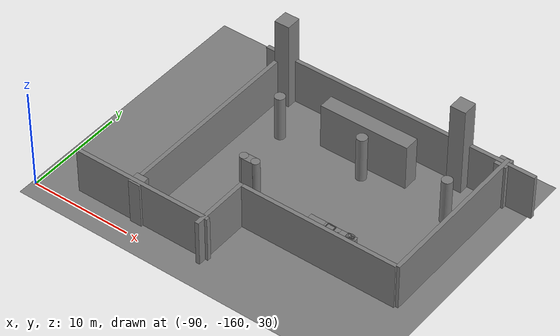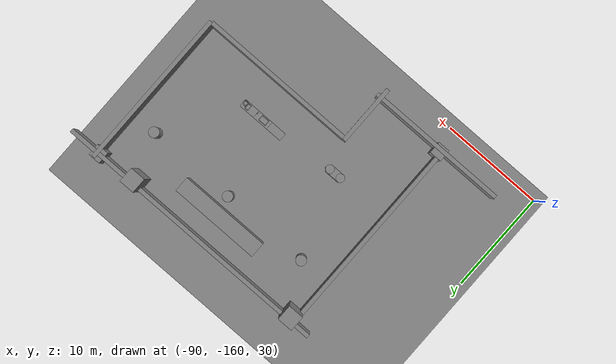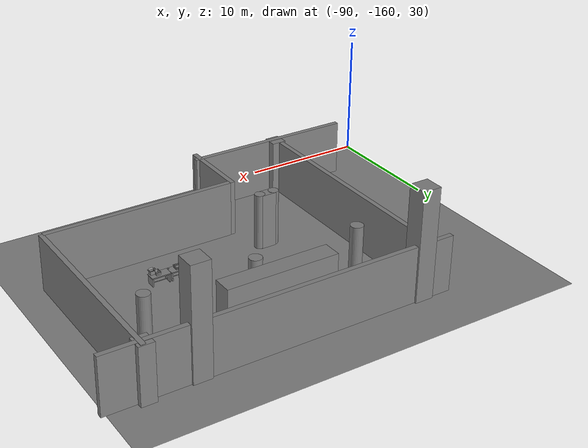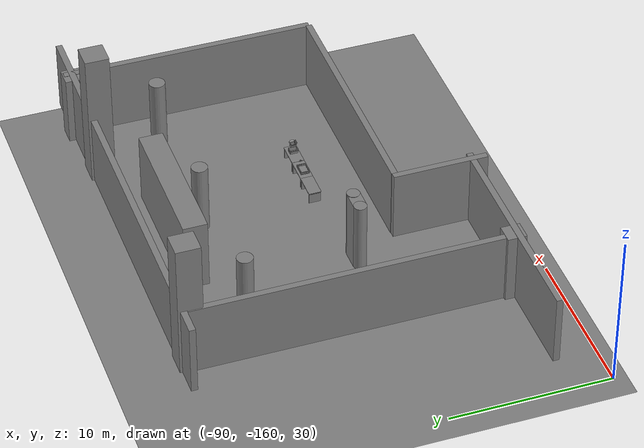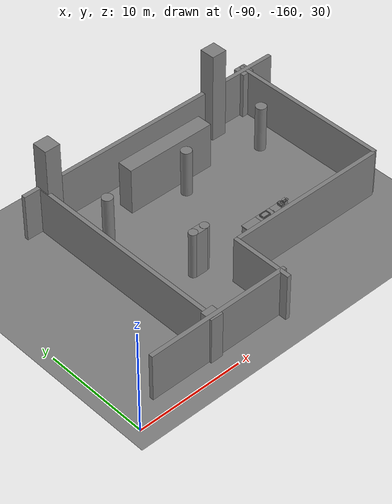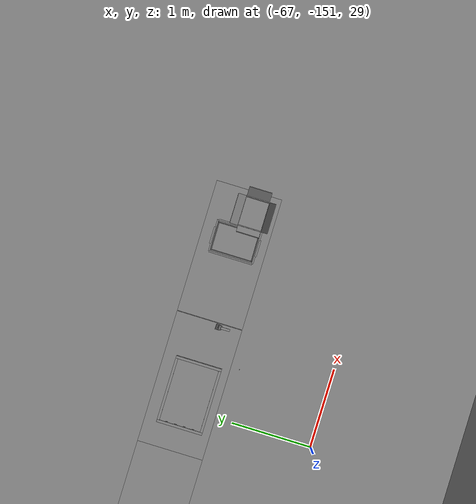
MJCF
<mujoco>
    <option gravity="0.000000000 0.000000000 -9.810000420" timestep="0.0049999999" integrator="implicitfast" density="1.225" viscosity="1.8000001e-05" noslip_iterations="10" iterations="100" sdf_iterations="50">
        <flag multiccd="disable"/>
    </option>
    <size memory="1000M"/>
    <compiler coordinate="local"/>
    <worldbody>
        <light cutoff="30" pos="0 1 1" dir="0 -1 -2"/>
        <light cutoff="30" pos="0 -1 1" dir="0 1 -2"/>
        <body pos="-64.866622925 -149.383972168 30.183746338" euler="89.999992371 89.999946594 0.000000000" name="openloong_gripper_2f85_fix_base_usda_bluebox_01">
            <geom contype="1" conaffinity="1" density="1000" type="box" material="" rgba="0.500000000 0.500000000 0.500000000 1.000000000" solimp="0.899999976 0.949999988 0.001000000" friction="1.000000000 0.005000000 0.000100000" solref="0.020000000 1.000000000" margin="0" condim="3" group="0" pos="0.276596069 0.187225342 0.000061035" quat="0.707107008 0.000077501 0.707106471 0.000077456" size="0.100000001 0.057999998 0.010000000" name="openloong_gripper_2f85_fix_base_usda_geom_2EA94CA7_1C4A_4EC6_B851_546676641EF6"/>
            <geom contype="1" conaffinity="1" density="1000" type="box" material="" rgba="0.500000000 0.500000000 0.500000000 1.000000000" solimp="0.899999976 0.949999988 0.001000000" friction="1.000000000 0.005000000 0.000100000" solref="0.020000000 1.000000000" margin="0" condim="3" group="0" pos="0.000000000 0.002883911 0.000000000" quat="1.000000000 0.000000000 0.000000000 0.000000000" size="0.254000008 0.003000000 0.172000006" name="openloong_gripper_2f85_fix_base_usda_geom_D5A056E2_8EA7_4D7F_A007_5A3413593A81"/>
            <geom contype="1" conaffinity="1" density="1000" type="box" material="" rgba="0.500000000 0.500000000 0.500000000 1.000000000" solimp="0.899999976 0.949999988 0.001000000" friction="1.000000000 0.005000000 0.000100000" solref="0.020000000 1.000000000" margin="0" condim="3" group="0" pos="0.000015259 0.124874115 0.173477173" quat="0.999796450 0.020176515 -0.000000015 0.000000030" size="0.259999990 0.119999997 0.007000000" name="openloong_gripper_2f85_fix_base_usda_geom_7020EA58_1C4D_4B2B_9C6C_C3C6B8036E91"/>
            <geom contype="1" conaffinity="1" density="1000" type="box" material="" rgba="0.500000000 0.500000000 0.500000000 1.000000000" solimp="0.899999976 0.949999988 0.001000000" friction="1.000000000 0.005000000 0.000100000" solref="0.020000000 1.000000000" margin="0" condim="3" group="0" pos="0.000015259 0.124874115 -0.173477173" quat="0.999796450 -0.020176545 -0.000000015 0.000000000" size="0.259999990 0.119999997 0.007000000" name="openloong_gripper_2f85_fix_base_usda_geom_0654FF07_F7AA_40C8_9465_CF6FFE050564"/>
            <geom contype="1" conaffinity="1" density="1000" type="box" material="" rgba="0.500000000 0.500000000 0.500000000 1.000000000" solimp="0.899999976 0.949999988 0.001000000" friction="1.000000000 0.005000000 0.000100000" solref="0.020000000 1.000000000" margin="0" condim="3" group="0" pos="0.000015259 0.214012146 0.188980103" quat="0.999913096 0.013176724 0.000000015 0.000000000" size="0.259999990 0.029999999 0.012500000" name="openloong_gripper_2f85_fix_base_usda_geom_557E6022_8051_4126_8EAF_37E91D642432"/>
            <geom contype="1" conaffinity="1" density="1000" type="box" material="" rgba="0.500000000 0.500000000 0.500000000 1.000000000" solimp="0.899999976 0.949999988 0.001000000" friction="1.000000000 0.005000000 0.000100000" solref="0.020000000 1.000000000" margin="0" condim="3" group="0" pos="-0.258346558 0.125289917 0.001876831" quat="0.702796996 -0.020792052 0.710783184 0.020769238" size="0.189999998 0.119999997 0.009000000" name="openloong_gripper_2f85_fix_base_usda_geom_CD31E93F_5C56_4ED9_8E34_C34F4454136B"/>
            <geom contype="1" conaffinity="1" density="1000" type="box" material="" rgba="0.500000000 0.500000000 0.500000000 1.000000000" solimp="0.899999976 0.949999988 0.001000000" friction="1.000000000 0.005000000 0.000100000" solref="0.020000000 1.000000000" margin="0" condim="3" group="0" pos="0.000015259 0.214012146 -0.188980103" quat="0.999913096 -0.013176769 0.000000030 0.000000015" size="0.259999990 0.029999999 0.012500000" name="openloong_gripper_2f85_fix_base_usda_geom_9378317F_E20A_4320_987C_29E712F8D40A"/>
            <geom contype="1" conaffinity="1" density="1000" type="box" material="" rgba="0.500000000 0.500000000 0.500000000 1.000000000" solimp="0.899999976 0.949999988 0.001000000" friction="1.000000000 0.005000000 0.000100000" solref="0.020000000 1.000000000" margin="0" condim="3" group="0" pos="-0.276596069 0.187225342 0.000061035" quat="0.707106650 0.000077441 0.707106709 0.000077456" size="0.100000001 0.057999998 0.010000000" name="openloong_gripper_2f85_fix_base_usda_geom_FB435430_D145_4358_89CA_826E15252C75"/>
            <geom contype="1" conaffinity="1" density="1000" type="box" material="" rgba="0.500000000 0.500000000 0.500000000 1.000000000" solimp="0.899999976 0.949999988 0.001000000" friction="1.000000000 0.005000000 0.000100000" solref="0.020000000 1.000000000" margin="0" condim="3" group="0" pos="0.258346558 0.125289917 0.001876831" quat="0.702851534 0.018856451 0.710823834 -0.019329429" size="0.189999998 0.119999997 0.009000000" name="openloong_gripper_2f85_fix_base_usda_geom_48E0CCE6_F270_4FE9_8370_983D9AF3BCA1"/>
            <freejoint name="openloong_gripper_2f85_fix_base_usda_bluebox_01_joint"/>
            <site size="0.005000000 0.005000000 0.005000000" rgba="0.500000000 0.500000000 0.500000000 1.000000000" pos="0.000000000 0.000000000 0.000000000" quat="0.999961913 0.008726534 0.000000000 0.000000000" group="0" type="sphere" name="openloong_gripper_2f85_fix_base_usda_bluebox_01site"/>
        </body>
        <body pos="-64.496299744 -149.491867065 30.235729218" euler="0.000000000 0.000000000 89.999946594" name="openloong_gripper_2f85_fix_base_usda_cardboardbox_01">
            <geom contype="1" conaffinity="1" density="1000" type="box" material="" rgba="0.500000000 0.500000000 0.500000000 1.000000000" solimp="0.899999976 0.949999988 0.001000000" friction="1.000000000 0.005000000 0.000100000" solref="0.020000000 1.000000000" margin="0" condim="3" group="0" pos="-0.003166199 -0.004086494 0.005052090" quat="1.000000000 0.000000000 0.000000000 0.000000000" size="0.142499998 0.177500010 0.005000000" name="openloong_gripper_2f85_fix_base_usda_geom_85FBA0C3_1445_43D8_966B_BDEA8E72E364"/>
            <geom contype="1" conaffinity="1" density="1000" type="box" material="" rgba="0.500000000 0.500000000 0.500000000 1.000000000" solimp="0.899999976 0.949999988 0.001000000" friction="1.000000000 0.005000000 0.000100000" solref="0.020000000 1.000000000" margin="0" condim="3" group="0" pos="-0.003166199 0.170316696 0.150570869" quat="1.000000000 0.000000000 0.000000000 0.000000000" size="0.142499998 0.005000000 0.149999991" name="openloong_gripper_2f85_fix_base_usda_geom_49FEDFBC_D7FF_4D2D_A989_2B598F7834EA"/>
            <geom contype="1" conaffinity="1" density="1000" type="box" material="" rgba="0.500000000 0.500000000 0.500000000 1.000000000" solimp="0.899999976 0.949999988 0.001000000" friction="1.000000000 0.005000000 0.000100000" solref="0.020000000 1.000000000" margin="0" condim="3" group="0" pos="-0.147399902 -0.005307198 0.150570869" quat="1.000000000 0.000000000 0.000000000 0.000000000" size="0.005000000 0.177500010 0.149999991" name="openloong_gripper_2f85_fix_base_usda_geom_8AD6D9C9_C313_4F7B_987D_6ACA12BB594C"/>
            <geom contype="1" conaffinity="1" density="1000" type="box" material="" rgba="0.500000000 0.500000000 0.500000000 1.000000000" solimp="0.899999976 0.949999988 0.001000000" friction="1.000000000 0.005000000 0.000100000" solref="0.020000000 1.000000000" margin="0" condim="3" group="0" pos="0.140275955 -0.005307198 0.150570869" quat="1.000000000 0.000000000 0.000000000 0.000000000" size="0.005000000 0.177500010 0.149999991" name="openloong_gripper_2f85_fix_base_usda_geom_974A62D4_A9E8_4423_B252_85B9BEA267ED"/>
            <geom contype="1" conaffinity="1" density="1000" type="box" material="" rgba="0.500000000 0.500000000 0.500000000 1.000000000" solimp="0.899999976 0.949999988 0.001000000" friction="1.000000000 0.005000000 0.000100000" solref="0.020000000 1.000000000" margin="0" condim="3" group="0" pos="-0.003166199 -0.181550980 0.150570869" quat="1.000000000 0.000000000 0.000000000 0.000000000" size="0.142499998 0.005000000 0.149999991" name="openloong_gripper_2f85_fix_base_usda_geom_4F3D4082_7500_4B4B_AC2F_E0081BAA2701"/>
            <freejoint name="openloong_gripper_2f85_fix_base_usda_cardboardbox_01_joint"/>
            <site size="0.005000000 0.005000000 0.005000000" rgba="0.500000000 0.500000000 0.500000000 1.000000000" pos="0.000000000 0.000000000 0.000000000" quat="0.999961913 0.008726535 0.000000000 0.000000000" group="0" type="sphere" name="openloong_gripper_2f85_fix_base_usda_site_A24CE30A_E77A_486E_BED6_EC3A10C0F51A"/>
            <body pos="0.139160156 -0.004048347 0.301930904" euler="-179.999954224 49.383502960 179.999954224" name="openloong_gripper_2f85_fix_base_usda_A1_006">
                <geom contype="1" conaffinity="1" density="1000" type="box" material="" rgba="0.500000000 0.500000000 0.500000000 1.000000000" solimp="0.899999976 0.949999988 0.001000000" friction="1.000000000 0.005000000 0.000100000" solref="0.020000000 1.000000000" margin="0" condim="3" group="0" pos="-0.071587563 0.000009537 0.001745224" quat="0.999999881 0.000000000 0.000000000 0.000000000" size="0.071249999 0.179999992 0.002500000" name="openloong_gripper_2f85_fix_base_usda_geom_7727C63E_DC4B_4490_A6C1_49EC206815DF"/>
                <joint armature="0" stiffness="0.07" damping="0.0099999998" axis="0.000000 1.000000 0.000000" type="hinge" name="openloong_gripper_2f85_fix_base_usda_A1_006"/>
            </body>
            <body pos="-0.145902634 -0.004086494 0.301938057" euler="-180.000000000 -60.000011444 -180.000000000" name="openloong_gripper_2f85_fix_base_usda_A2_006">
                <geom contype="1" conaffinity="1" density="1000" type="box" material="" rgba="0.500000000 0.500000000 0.500000000 1.000000000" solimp="0.899999976 0.949999988 0.001000000" friction="1.000000000 0.005000000 0.000100000" solref="0.020000000 1.000000000" margin="0" condim="3" group="0" pos="0.071268082 0.000009537 0.002717972" quat="0.000002921 0.000000000 -0.000000030 0.999999881" size="0.071249999 0.179999992 0.002500000" name="openloong_gripper_2f85_fix_base_usda_geom_CEB3A042_99C6_445C_A76A_547A524AFC18"/>
                <joint armature="0" stiffness="0.07" damping="0.0099999998" axis="0.000000 1.000000 0.000000" type="hinge" name="openloong_gripper_2f85_fix_base_usda_A2_006"/>
            </body>
            <body pos="-0.003385544 0.175991058 0.301930904" euler="-125.858116150 -0.000004561 0.000002331" name="openloong_gripper_2f85_fix_base_usda_B2_006">
                <geom contype="1" conaffinity="1" density="1000" type="box" material="" rgba="0.500000000 0.500000000 0.500000000 1.000000000" solimp="0.899999976 0.949999988 0.001000000" friction="1.000000000 0.005000000 0.000100000" solref="0.020000000 1.000000000" margin="0" condim="3" group="0" pos="0.000009537 -0.070939064 -0.002470016" quat="0.999614120 0.027776197 -0.000000015 0.000000030" size="0.137500003 0.064999998 0.005000000" name="openloong_gripper_2f85_fix_base_usda_geom_5930A369_109B_40AB_AB34_278399EC5E70"/>
                <joint armature="0" stiffness="0.07" damping="0.0099999998" axis="1.000000 0.000000 0.000000" type="hinge" name="openloong_gripper_2f85_fix_base_usda_B2_006"/>
            </body>
            <body pos="-0.003385544 -0.184140205 0.301938057" euler="147.805557251 0.000000000 0.000000000" name="openloong_gripper_2f85_fix_base_usda_B1_006">
                <geom contype="1" conaffinity="1" density="1000" type="box" material="" rgba="0.500000000 0.500000000 0.500000000 1.000000000" solimp="0.899999976 0.949999988 0.001000000" friction="1.000000000 0.005000000 0.000100000" solref="0.020000000 1.000000000" margin="0" condim="3" group="0" pos="-0.000028610 0.070202351 -0.002703667" quat="0.999614179 -0.027776167 0.000000000 0.000000000" size="0.137500003 0.064999998 0.005000000" name="openloong_gripper_2f85_fix_base_usda_geom_588F218B_57CC_4DD3_B938_EE83E699F6E5"/>
                <joint armature="0" stiffness="0.07" damping="0.0099999998" axis="1.000000 0.000000 0.000000" type="hinge" name="openloong_gripper_2f85_fix_base_usda_B1_006"/>
            </body>
        </body>
        <body pos="-65.882858276 -149.481979370 30.229999542" euler="-64.487716675 0.000000000 0.000000000" name="openloong_gripper_2f85_fix_base_usda_Barcode">
            <geom contype="1" conaffinity="1" density="1000" type="box" material="" rgba="0.500000000 0.500000000 0.500000000 1.000000000" solimp="0.899999976 0.949999988 0.001000000" friction="1.000000000 0.005000000 0.000100000" solref="0.020000000 1.000000000" margin="0" condim="3" group="0" pos="0.000000000 0.013038635 0.001419067" quat="0.000000000 0.000000000 0.000000000 1.000000119" size="0.034000002 0.010000000 0.017999999" name="openloong_gripper_2f85_fix_base_usda_geom_96F79A09_2A2C_4859_AE21_B3C6BE29DA93"/>
            <geom contype="1" conaffinity="1" density="1000" type="box" material="" rgba="0.500000000 0.500000000 0.500000000 1.000000000" solimp="0.899999976 0.949999988 0.001000000" friction="1.000000000 0.005000000 0.000100000" solref="0.020000000 1.000000000" margin="0" condim="3" group="0" pos="0.000000000 -0.035301208 -0.007095337" quat="0.000000000 0.000000000 -0.043619365 0.999048233" size="0.028999999 0.010000000 0.020000000" name="openloong_gripper_2f85_fix_base_usda_geom_961BF789_5285_4646_AB89_22A3087B6BC5"/>
            <geom contype="1" conaffinity="1" density="1000" type="box" material="" rgba="0.500000000 0.500000000 0.500000000 1.000000000" solimp="0.899999976 0.949999988 0.001000000" friction="1.000000000 0.005000000 0.000100000" solref="0.020000000 1.000000000" margin="0" condim="3" group="0" pos="0.000000000 -0.043411255 -0.011749268" quat="0.922262907 0.386563420 0.000000000 0.000000000" size="0.026000001 0.010000000 0.020000000" name="openloong_gripper_2f85_fix_base_usda_geom_947FF679_DF7A_40F6_A933_4A736E356946"/>
            <geom contype="1" conaffinity="1" density="1000" type="box" material="" rgba="0.500000000 0.500000000 0.500000000 1.000000000" solimp="0.899999976 0.949999988 0.001000000" friction="1.000000000 0.005000000 0.000100000" solref="0.020000000 1.000000000" margin="0" condim="3" group="0" pos="0.000000000 -0.016967773 -0.031860352" quat="0.000000000 0.000000000 0.000000000 1.000000119" size="0.008000000 0.010000000 0.013000000" name="openloong_gripper_2f85_fix_base_usda_geom_A01E77C7_3B16_4C95_84DA_2DB1E4940331"/>
            <geom contype="1" conaffinity="1" density="1000" type="box" material="" rgba="0.500000000 0.500000000 0.500000000 1.000000000" solimp="0.899999976 0.949999988 0.001000000" friction="1.000000000 0.005000000 0.000100000" solref="0.020000000 1.000000000" margin="0" condim="3" group="0" pos="0.000000000 -0.001869202 0.000312805" quat="0.953716993 0.300705761 0.000000000 0.000000000" size="0.032000002 0.010000000 0.018999999" name="openloong_gripper_2f85_fix_base_usda_geom_7C7E2FEA_D1FD_4BF5_98F1_14831C716E3D"/>
            <geom contype="1" conaffinity="1" density="1000" type="box" material="" rgba="0.500000000 0.500000000 0.500000000 1.000000000" solimp="0.899999976 0.949999988 0.001000000" friction="1.000000000 0.005000000 0.000100000" solref="0.020000000 1.000000000" margin="0" condim="3" group="0" pos="0.000000000 -0.019531250 -0.003173828" quat="0.953716993 0.300705761 0.000000000 0.000000000" size="0.030999999 0.010000000 0.020000000" name="openloong_gripper_2f85_fix_base_usda_geom_2CA79469_52CA_4DEB_8917_C6946C807E97"/>
            <geom contype="1" conaffinity="1" density="1000" type="box" material="" rgba="0.500000000 0.500000000 0.500000000 1.000000000" solimp="0.899999976 0.949999988 0.001000000" friction="1.000000000 0.005000000 0.000100000" solref="0.020000000 1.000000000" margin="0" condim="3" group="0" pos="0.000000000 -0.035301208 -0.007095337" quat="0.953716993 0.300705761 0.000000000 0.000000000" size="0.028999999 0.010000000 0.020000000" name="openloong_gripper_2f85_fix_base_usda_geom_03B1DE81_2765_4014_849E_9FBA07F382D7"/>
            <geom contype="1" conaffinity="1" density="1000" type="box" material="" rgba="0.500000000 0.500000000 0.500000000 1.000000000" solimp="0.899999976 0.949999988 0.001000000" friction="1.000000000 0.005000000 0.000100000" solref="0.020000000 1.000000000" margin="0" condim="3" group="0" pos="0.000000000 -0.042617798 -0.071121216" quat="0.000000000 0.000000000 0.000000000 1.000000119" size="0.013000000 0.021000000 0.059999999" name="openloong_gripper_2f85_fix_base_usda_geom_D57E18F0_3BD2_466A_AA6F_0BD9644841CB"/>
            <freejoint name="openloong_gripper_2f85_fix_base_usda_Barcode_joint"/>
            <site size="0.005000000 0.005000000 0.005000000" rgba="0.500000000 0.500000000 0.500000000 1.000000000" pos="0.000000000 0.000000000 0.000000000" quat="1.000000000 0.000000000 0.000000000 0.000000000" group="0" type="sphere" name="openloong_gripper_2f85_fix_base_usda_Barcode_site"/>
        </body>
        <body pos="-66.745018005 -149.392349243 30.184000015" euler="0.000000000 0.000000000 89.999946594" name="[22330613400148]_Basket_01">
            <geom contype="1" conaffinity="1" density="1000" type="box" material="" rgba="0.500000000 0.500000000 0.500000000 1.000000000" solimp="0.899999976 0.949999988 0.001000000" friction="1.000000000 0.005000000 0.000100000" solref="0.020000000 1.000000000" margin="0" condim="3" group="0" pos="-0.052425385 0.389207840 0.089787483" quat="0.707107008 0.000000000 0.000000000 0.707106411" size="0.014249999 0.014249999 0.059999999" name="[22330613400148]_geom_94FF81D0_65DD_4306_BE85_143BE6501BD3"/>
            <geom contype="1" conaffinity="1" density="1000" type="box" material="" rgba="0.500000000 0.500000000 0.500000000 1.000000000" solimp="0.899999976 0.949999988 0.001000000" friction="1.000000000 0.005000000 0.000100000" solref="0.020000000 1.000000000" margin="0" condim="3" group="0" pos="0.264015198 -0.133043289 0.089787483" quat="0.707107008 0.000000000 0.000000000 0.707106411" size="0.014249999 0.014249999 0.059999999" name="[22330613400148]_geom_BA42D268_0122_4BBF_A1AD_EDCC21C511AE"/>
            <geom contype="1" conaffinity="1" density="1000" type="box" material="" rgba="0.500000000 0.500000000 0.500000000 1.000000000" solimp="0.899999976 0.949999988 0.001000000" friction="1.000000000 0.005000000 0.000100000" solref="0.020000000 1.000000000" margin="0" condim="3" group="0" pos="-0.264015198 -0.265548706 0.089793205" quat="0.707107008 0.000000000 0.000000000 0.707106411" size="0.014249999 0.014249999 0.059999999" name="[22330613400148]_geom_64FC775E_EC99_4FB1_B8B2_7BF9B13CC03A"/>
            <geom contype="1" conaffinity="1" density="1000" type="box" material="" rgba="0.500000000 0.500000000 0.500000000 1.000000000" solimp="0.899999976 0.949999988 0.001000000" friction="1.000000000 0.005000000 0.000100000" solref="0.020000000 1.000000000" margin="0" condim="3" group="0" pos="-0.160263062 -0.389322281 0.089793205" quat="0.707107008 0.000000000 0.000000000 0.707106411" size="0.014249999 0.014249999 0.059999999" name="[22330613400148]_geom_1EFB6B65_2D8C_430A_84AD_FD5D9A34F4FF"/>
            <geom contype="1" conaffinity="1" density="1000" type="box" material="" rgba="0.500000000 0.500000000 0.500000000 1.000000000" solimp="0.899999976 0.949999988 0.001000000" friction="1.000000000 0.005000000 0.000100000" solref="0.020000000 1.000000000" margin="0" condim="3" group="0" pos="0.162265778 -0.389322281 0.089787483" quat="0.707107008 0.000000000 0.000000000 0.707106411" size="0.014249999 0.014249999 0.059999999" name="[22330613400148]_geom_2B610CAD_2B67_4D5B_888C_694BD9AA9E2C"/>
            <geom contype="1" conaffinity="1" density="1000" type="box" material="" rgba="0.500000000 0.500000000 0.500000000 1.000000000" solimp="0.899999976 0.949999988 0.001000000" friction="1.000000000 0.005000000 0.000100000" solref="0.020000000 1.000000000" margin="0" condim="3" group="0" pos="0.264015198 0.389207840 0.089787483" quat="0.707107008 0.000000000 0.000000000 0.707106411" size="0.014249999 0.014249999 0.059999999" name="[22330613400148]_geom_8D34DD0A_B6AF_4209_B44E_AE2C014F1703"/>
            <geom contype="1" conaffinity="1" density="1000" type="box" material="" rgba="0.500000000 0.500000000 0.500000000 1.000000000" solimp="0.899999976 0.949999988 0.001000000" friction="1.000000000 0.005000000 0.000100000" solref="0.020000000 1.000000000" margin="0" condim="3" group="0" pos="-0.264015198 -0.133043289 0.089793205" quat="0.707107008 0.000000000 0.000000000 0.707106411" size="0.014249999 0.014249999 0.059999999" name="[22330613400148]_geom_7AA5833E_DFBC_495D_BD94_1F29553069CD"/>
            <geom contype="1" conaffinity="1" density="1000" type="box" material="" rgba="0.500000000 0.500000000 0.500000000 1.000000000" solimp="0.899999976 0.949999988 0.001000000" friction="1.000000000 0.005000000 0.000100000" solref="0.020000000 1.000000000" margin="0" condim="3" group="0" pos="-0.264026642 0.269256592 0.089793205" quat="0.707107008 0.000000000 0.000000000 0.707106411" size="0.014249999 0.014249999 0.059999999" name="[22330613400148]_geom_275C70FC_B9C8_4A82_814D_2C9ADDC831C8"/>
            <geom contype="1" conaffinity="1" density="1000" type="box" material="" rgba="0.500000000 0.500000000 0.500000000 1.000000000" solimp="0.899999976 0.949999988 0.001000000" friction="1.000000000 0.005000000 0.000100000" solref="0.020000000 1.000000000" margin="0" condim="3" group="0" pos="0.054462433 0.389207840 0.089787483" quat="0.707107008 0.000000000 0.000000000 0.707106411" size="0.014249999 0.014249999 0.059999999" name="[22330613400148]_geom_6A7F7436_7160_454A_A34F_061C04B2AC6B"/>
            <geom contype="1" conaffinity="1" density="1000" type="box" material="" rgba="0.500000000 0.500000000 0.500000000 1.000000000" solimp="0.899999976 0.949999988 0.001000000" friction="1.000000000 0.005000000 0.000100000" solref="0.020000000 1.000000000" margin="0" condim="3" group="0" pos="0.054462433 -0.389322281 0.089787483" quat="0.707107008 0.000000000 0.000000000 0.707106411" size="0.014249999 0.014249999 0.059999999" name="[22330613400148]_geom_6BDC419B_A04A_41E1_AD7F_C2A219E3AC2E"/>
            <geom contype="1" conaffinity="1" density="1000" type="box" material="" rgba="0.500000000 0.500000000 0.500000000 1.000000000" solimp="0.899999976 0.949999988 0.001000000" friction="1.000000000 0.005000000 0.000100000" solref="0.020000000 1.000000000" margin="0" condim="3" group="0" pos="0.264015198 0.269256592 0.089793205" quat="0.707107008 0.000000000 0.000000000 0.707106411" size="0.014249999 0.014249999 0.059999999" name="[22330613400148]_geom_3DA507F1_9D4D_40F7_86A9_4D6A53870223"/>
            <geom contype="1" conaffinity="1" density="1000" type="box" material="" rgba="0.500000000 0.500000000 0.500000000 1.000000000" solimp="0.899999976 0.949999988 0.001000000" friction="1.000000000 0.005000000 0.000100000" solref="0.020000000 1.000000000" margin="0" condim="3" group="0" pos="0.264015198 -0.389322281 0.089787483" quat="0.707107008 0.000000000 0.000000000 0.707106411" size="0.014249999 0.014249999 0.059999999" name="[22330613400148]_geom_D3CDAF0E_2430_48D3_8FCB_EBA6873C0992"/>
            <geom contype="1" conaffinity="1" density="1000" type="box" material="" rgba="0.500000000 0.500000000 0.500000000 1.000000000" solimp="0.899999976 0.949999988 0.001000000" friction="1.000000000 0.005000000 0.000100000" solref="0.020000000 1.000000000" margin="0" condim="3" group="0" pos="0.000000000 0.000000000 0.015998840" quat="0.707107008 0.000000000 0.000000000 0.707106411" size="0.403499991 0.279000014 0.015750000" name="[22330613400148]_geom_E4470207_E434_4BEC_ABF1_CDC546CE4518"/>
            <geom contype="1" conaffinity="1" density="1000" type="box" material="" rgba="0.500000000 0.500000000 0.500000000 1.000000000" solimp="0.899999976 0.949999988 0.001000000" friction="1.000000000 0.005000000 0.000100000" solref="0.020000000 1.000000000" margin="0" condim="3" group="0" pos="0.000000000 -0.389476776 0.163619041" quat="0.707107008 0.000000000 0.000000000 0.707106411" size="0.015000000 0.277500004 0.015750000" name="[22330613400148]_geom_A844CC19_D7BF_4DEE_93A7_CD64B2844F85"/>
            <geom contype="1" conaffinity="1" density="1000" type="box" material="" rgba="0.500000000 0.500000000 0.500000000 1.000000000" solimp="0.899999976 0.949999988 0.001000000" friction="1.000000000 0.005000000 0.000100000" solref="0.020000000 1.000000000" margin="0" condim="3" group="0" pos="0.162265778 0.389207840 0.089787483" quat="0.707107008 0.000000000 0.000000000 0.707106411" size="0.014249999 0.014249999 0.059999999" name="[22330613400148]_geom_B8B42A0B_8576_434C_ACD4_B55DDCC523EB"/>
            <geom contype="1" conaffinity="1" density="1000" type="box" material="" rgba="0.500000000 0.500000000 0.500000000 1.000000000" solimp="0.899999976 0.949999988 0.001000000" friction="1.000000000 0.005000000 0.000100000" solref="0.020000000 1.000000000" margin="0" condim="3" group="0" pos="0.000000000 0.389471054 0.163619041" quat="0.707107008 0.000000000 0.000000000 0.707106411" size="0.015000000 0.277500004 0.015750000" name="[22330613400148]_geom_E9ADE931_E6A9_45AE_8590_9669A7D00A2B"/>
            <geom contype="1" conaffinity="1" density="1000" type="box" material="" rgba="0.500000000 0.500000000 0.500000000 1.000000000" solimp="0.899999976 0.949999988 0.001000000" friction="1.000000000 0.005000000 0.000100000" solref="0.020000000 1.000000000" margin="0" condim="3" group="0" pos="-0.263511658 0.000000000 0.163619041" quat="0.707107008 0.000000000 0.000000000 0.707106411" size="0.403499991 0.015000000 0.015750000" name="[22330613400148]_geom_34B794E2_F067_4A58_8652_EAF9279646F4"/>
            <geom contype="1" conaffinity="1" density="1000" type="box" material="" rgba="0.500000000 0.500000000 0.500000000 1.000000000" solimp="0.899999976 0.949999988 0.001000000" friction="1.000000000 0.005000000 0.000100000" solref="0.020000000 1.000000000" margin="0" condim="3" group="0" pos="-0.264015198 0.141334534 0.089793205" quat="0.707107008 0.000000000 0.000000000 0.707106411" size="0.014249999 0.014249999 0.059999999" name="[22330613400148]_geom_97AD2E80_6015_4F80_B59C_B5C5908A3661"/>
            <geom contype="1" conaffinity="1" density="1000" type="box" material="" rgba="0.500000000 0.500000000 0.500000000 1.000000000" solimp="0.899999976 0.949999988 0.001000000" friction="1.000000000 0.005000000 0.000100000" solref="0.020000000 1.000000000" margin="0" condim="3" group="0" pos="0.264015198 -0.265548706 0.089787483" quat="0.707107008 0.000000000 0.000000000 0.707106411" size="0.014249999 0.014249999 0.059999999" name="[22330613400148]_geom_C883A515_56C7_4DB3_AC55_F58E5FCA4117"/>
            <geom contype="1" conaffinity="1" density="1000" type="box" material="" rgba="0.500000000 0.500000000 0.500000000 1.000000000" solimp="0.899999976 0.949999988 0.001000000" friction="1.000000000 0.005000000 0.000100000" solref="0.020000000 1.000000000" margin="0" condim="3" group="0" pos="-0.160263062 0.389207840 0.089787483" quat="0.707107008 0.000000000 0.000000000 0.707106411" size="0.014249999 0.014249999 0.059999999" name="[22330613400148]_geom_48E717C9_5DBB_46D2_B740_607EA1F76609"/>
            <geom contype="1" conaffinity="1" density="1000" type="box" material="" rgba="0.500000000 0.500000000 0.500000000 1.000000000" solimp="0.899999976 0.949999988 0.001000000" friction="1.000000000 0.005000000 0.000100000" solref="0.020000000 1.000000000" margin="0" condim="3" group="0" pos="-0.052425385 -0.389322281 0.089787483" quat="0.707107008 0.000000000 0.000000000 0.707106411" size="0.014249999 0.014249999 0.059999999" name="[22330613400148]_geom_A2677BFD_5B07_4EC9_9F4B_DFA5DEB66792"/>
            <geom contype="1" conaffinity="1" density="1000" type="box" material="" rgba="0.500000000 0.500000000 0.500000000 1.000000000" solimp="0.899999976 0.949999988 0.001000000" friction="1.000000000 0.005000000 0.000100000" solref="0.020000000 1.000000000" margin="0" condim="3" group="0" pos="-0.264026642 -0.389322281 0.089793205" quat="0.707107008 0.000000000 0.000000000 0.707106411" size="0.014249999 0.014249999 0.059999999" name="[22330613400148]_geom_E5F98CA7_43A8_48E0_B8C6_CCEC1BA3E936"/>
            <geom contype="1" conaffinity="1" density="1000" type="box" material="" rgba="0.500000000 0.500000000 0.500000000 1.000000000" solimp="0.899999976 0.949999988 0.001000000" friction="1.000000000 0.005000000 0.000100000" solref="0.020000000 1.000000000" margin="0" condim="3" group="0" pos="0.264015198 0.141334534 0.089787483" quat="0.707107008 0.000000000 0.000000000 0.707106411" size="0.014249999 0.014249999 0.059999999" name="[22330613400148]_geom_65A5C980_CC69_41B9_80E3_887BAEC1305D"/>
            <geom contype="1" conaffinity="1" density="1000" type="box" material="" rgba="0.500000000 0.500000000 0.500000000 1.000000000" solimp="0.899999976 0.949999988 0.001000000" friction="1.000000000 0.005000000 0.000100000" solref="0.020000000 1.000000000" margin="0" condim="3" group="0" pos="-0.264015198 0.389207840 0.089793205" quat="0.707107008 0.000000000 0.000000000 0.707106411" size="0.014249999 0.014249999 0.059999999" name="[22330613400148]_geom_24206A26_0408_4656_BA54_E8D3A8F09BBA"/>
            <geom contype="1" conaffinity="1" density="1000" type="box" material="" rgba="0.500000000 0.500000000 0.500000000 1.000000000" solimp="0.899999976 0.949999988 0.001000000" friction="1.000000000 0.005000000 0.000100000" solref="0.020000000 1.000000000" margin="0" condim="3" group="0" pos="0.264015198 0.004480362 0.089787483" quat="0.707107008 0.000000000 0.000000000 0.707106411" size="0.014249999 0.014249999 0.059999999" name="[22330613400148]_geom_605C7B94_F9CE_46BE_AF2D_AFE335CD1BF7"/>
            <geom contype="1" conaffinity="1" density="1000" type="box" material="" rgba="0.500000000 0.500000000 0.500000000 1.000000000" solimp="0.899999976 0.949999988 0.001000000" friction="1.000000000 0.005000000 0.000100000" solref="0.020000000 1.000000000" margin="0" condim="3" group="0" pos="0.263694763 -0.000011444 0.163619041" quat="0.707107008 0.000000000 0.000000000 0.707106411" size="0.403499991 0.015000000 0.015750000" name="[22330613400148]_geom_3BDEE3CB_26F2_4906_86D5_C890546CBDF9"/>
            <geom contype="1" conaffinity="1" density="1000" type="box" material="" rgba="0.500000000 0.500000000 0.500000000 1.000000000" solimp="0.899999976 0.949999988 0.001000000" friction="1.000000000 0.005000000 0.000100000" solref="0.020000000 1.000000000" margin="0" condim="3" group="0" pos="-0.264015198 0.004480362 0.089793205" quat="0.707107008 0.000000000 0.000000000 0.707106411" size="0.014249999 0.014249999 0.059999999" name="[22330613400148]_geom_1A7CEAFA_D94A_4FC1_B978_12463E276CD1"/>
            <freejoint name="[22330613400148]_joint_F33332DC_AA47_436A_89EA_DD28E1F632A9"/>
        </body>
        <body pos="0.000000000 0.000000000 0.000000000" euler="0.000000000 0.000000000 0.000000000" name="Static Objects_Static Objects">
            <geom contype="1" conaffinity="1" density="1000" type="box" material="" rgba="0.500000000 0.500000000 0.500000000 1.000000000" solimp="0.899999976 0.949999988 0.001000000" friction="1.000000000 0.005000000 0.000100000" solref="0.020000000 1.000000000" margin="0" condim="3" group="0" pos="-67.544113159 -149.365814209 29.727830887" quat="0.500000417 0.499999970 0.499999553 0.499999970" size="0.381000012 0.319999993 0.041000001" name="Static Objects_geom_A233FDBE_A6D2_40FD_8B72_DE25E6EF0BA4"/>
            <geom contype="1" conaffinity="1" density="1000" type="box" material="" rgba="0.500000000 0.500000000 0.500000000 1.000000000" solimp="0.899999976 0.949999988 0.001000000" friction="1.000000000 0.005000000 0.000100000" solref="0.020000000 1.000000000" margin="0" condim="3" group="0" pos="-68.239501953 -149.365814209 30.086868286" quat="0.500000417 0.499999970 0.499999553 0.499999970" size="0.370999992 0.039500002 0.745000005" name="Static Objects_geom_D58261C8_F78F_4F10_9C6C_B112EE697E31"/>
            <geom contype="1" conaffinity="1" density="1000" type="box" material="" rgba="0.500000000 0.500000000 0.500000000 1.000000000" solimp="0.899999976 0.949999988 0.001000000" friction="1.000000000 0.005000000 0.000100000" solref="0.020000000 1.000000000" margin="0" condim="3" group="0" pos="-68.239501953 -149.365814209 30.147235870" quat="0.500000417 0.499999970 0.499999553 0.499999970" size="0.400000006 0.022000000 0.800000012" name="Static Objects_geom_5698067A_1AB1_44DB_8D81_71007C0A44C9"/>
            <geom contype="1" conaffinity="1" density="1000" type="box" material="" rgba="0.500000000 0.500000000 0.500000000 1.000000000" solimp="0.899999976 0.949999988 0.001000000" friction="1.000000000 0.005000000 0.000100000" solref="0.020000000 1.000000000" margin="0" condim="3" group="0" pos="-68.934890747 -149.365814209 29.727830887" quat="0.500000417 0.499999970 0.499999553 0.499999970" size="0.381000012 0.319999993 0.041000001" name="Static Objects_geom_F70F1122_8E69_4BE3_9FF1_FF59175B6295"/>
            <geom contype="1" conaffinity="1" density="1000" type="box" material="" rgba="0.500000000 0.500000000 0.500000000 1.000000000" solimp="0.899999976 0.949999988 0.001000000" friction="1.000000000 0.005000000 0.000100000" solref="0.020000000 1.000000000" margin="0" condim="3" group="0" pos="-68.239501953 -149.365814209 29.561563492" quat="0.500000417 0.499999970 0.499999553 0.499999970" size="0.020000000 0.022000000 0.660000026" name="Static Objects_geom_CBBB049F_197C_4B6C_82E7_153DEA552286"/>
            <geom contype="1" conaffinity="1" density="1000" type="box" material="" rgba="0.500000000 0.500000000 0.500000000 1.000000000" solimp="0.899999976 0.949999988 0.001000000" friction="1.000000000 0.005000000 0.000100000" solref="0.020000000 1.000000000" margin="0" condim="3" group="0" pos="-65.945671082 -149.365814209 29.727830887" quat="0.500000417 0.499999970 0.499999553 0.499999970" size="0.381000012 0.319999993 0.041000001" name="Static Objects_geom_81AB5074_DCA5_42A0_8507_993B1EFD26C2"/>
            <geom contype="1" conaffinity="1" density="1000" type="box" material="" rgba="0.500000000 0.500000000 0.500000000 1.000000000" solimp="0.899999976 0.949999988 0.001000000" friction="1.000000000 0.005000000 0.000100000" solref="0.020000000 1.000000000" margin="0" condim="3" group="0" pos="-66.641059875 -149.365814209 30.086868286" quat="0.500000417 0.499999970 0.499999553 0.499999970" size="0.370999992 0.039500002 0.745000005" name="Static Objects_geom_4DC583B9_2E5B_42B2_9370_D4E328BA2906"/>
            <geom contype="1" conaffinity="1" density="1000" type="box" material="" rgba="0.500000000 0.500000000 0.500000000 1.000000000" solimp="0.899999976 0.949999988 0.001000000" friction="1.000000000 0.005000000 0.000100000" solref="0.020000000 1.000000000" margin="0" condim="3" group="0" pos="-66.641059875 -149.365814209 30.147235870" quat="0.500000417 0.499999970 0.499999553 0.499999970" size="0.400000006 0.022000000 0.800000012" name="Static Objects_geom_43A91A7D_A6EE_48CA_9BD5_FE773E251604"/>
            <geom contype="1" conaffinity="1" density="1000" type="box" material="" rgba="0.500000000 0.500000000 0.500000000 1.000000000" solimp="0.899999976 0.949999988 0.001000000" friction="1.000000000 0.005000000 0.000100000" solref="0.020000000 1.000000000" margin="0" condim="3" group="0" pos="-67.336448669 -149.365814209 29.727830887" quat="0.500000417 0.499999970 0.499999553 0.499999970" size="0.381000012 0.319999993 0.041000001" name="Static Objects_geom_9E733161_0441_40FF_8D78_9FBE3BD7A7C1"/>
            <geom contype="1" conaffinity="1" density="1000" type="box" material="" rgba="0.500000000 0.500000000 0.500000000 1.000000000" solimp="0.899999976 0.949999988 0.001000000" friction="1.000000000 0.005000000 0.000100000" solref="0.020000000 1.000000000" margin="0" condim="3" group="0" pos="-66.641059875 -149.365814209 29.561563492" quat="0.500000417 0.499999970 0.499999553 0.499999970" size="0.020000000 0.022000000 0.660000026" name="Static Objects_geom_6FDFB4C7_BE97_4543_B603_657E135E1942"/>
            <geom contype="1" conaffinity="1" density="1000" type="box" material="" rgba="0.500000000 0.500000000 0.500000000 1.000000000" solimp="0.899999976 0.949999988 0.001000000" friction="1.000000000 0.005000000 0.000100000" solref="0.020000000 1.000000000" margin="0" condim="3" group="0" pos="-64.338577271 -149.365814209 29.727830887" quat="0.500000417 0.499999970 0.499999553 0.499999970" size="0.381000012 0.319999993 0.041000001" name="Static Objects_geom_CFAE62B5_E742_42E0_B59E_E5CF3404279B"/>
            <geom contype="1" conaffinity="1" density="1000" type="box" material="" rgba="0.500000000 0.500000000 0.500000000 1.000000000" solimp="0.899999976 0.949999988 0.001000000" friction="1.000000000 0.005000000 0.000100000" solref="0.020000000 1.000000000" margin="0" condim="3" group="0" pos="-65.033966064 -149.365814209 30.086868286" quat="0.500000417 0.499999970 0.499999553 0.499999970" size="0.370999992 0.039500002 0.745000005" name="Static Objects_geom_B198396D_9BDB_4DE6_ABE4_5F4C3DCE6559"/>
            <geom contype="1" conaffinity="1" density="1000" type="box" material="" rgba="0.500000000 0.500000000 0.500000000 1.000000000" solimp="0.899999976 0.949999988 0.001000000" friction="1.000000000 0.005000000 0.000100000" solref="0.020000000 1.000000000" margin="0" condim="3" group="0" pos="-65.033966064 -149.365814209 30.147235870" quat="0.500000417 0.499999970 0.499999553 0.499999970" size="0.400000006 0.022000000 0.800000012" name="Static Objects_geom_38A9A613_49C1_4C41_966C_E2E223174614"/>
            <geom contype="1" conaffinity="1" density="1000" type="box" material="" rgba="0.500000000 0.500000000 0.500000000 1.000000000" solimp="0.899999976 0.949999988 0.001000000" friction="1.000000000 0.005000000 0.000100000" solref="0.020000000 1.000000000" margin="0" condim="3" group="0" pos="-65.729354858 -149.365814209 29.727830887" quat="0.500000417 0.499999970 0.499999553 0.499999970" size="0.381000012 0.319999993 0.041000001" name="Static Objects_geom_CE32276C_8A0F_4161_A329_0FB720E80230"/>
            <geom contype="1" conaffinity="1" density="1000" type="box" material="" rgba="0.500000000 0.500000000 0.500000000 1.000000000" solimp="0.899999976 0.949999988 0.001000000" friction="1.000000000 0.005000000 0.000100000" solref="0.020000000 1.000000000" margin="0" condim="3" group="0" pos="-65.033966064 -149.365814209 29.561563492" quat="0.500000417 0.499999970 0.499999553 0.499999970" size="0.020000000 0.022000000 0.660000026" name="Static Objects_geom_FF11DAF7_2E95_4860_8C63_2CF3A59216AB"/>
            <geom contype="1" conaffinity="1" density="1000" type="box" material="" rgba="0.500000000 0.500000000 0.500000000 1.000000000" solimp="0.899999976 0.949999988 0.001000000" friction="1.000000000 0.005000000 0.000100000" solref="0.020000000 1.000000000" margin="0" condim="3" group="0" pos="-61.754566193 -137.853729248 33.906845093" quat="0.707107067 0.000000000 0.000000000 0.707106471" size="0.759999990 0.759999990 4.500000000" name="Static Objects_geom_EA8CE02C_2862_40DD_8CC1_F48D0312799F"/>
            <geom contype="1" conaffinity="1" density="1000" type="box" material="" rgba="0.500000000 0.500000000 0.500000000 1.000000000" solimp="0.899999976 0.949999988 0.001000000" friction="1.000000000 0.005000000 0.000100000" solref="0.020000000 1.000000000" margin="0" condim="3" group="0" pos="-57.511135101 -144.927108765 31.707921982" quat="1.000000000 0.000000000 0.000000000 0.000000000" size="0.200000003 8.000000000 2.299999952" name="Static Objects_geom_21355886_AA8C_4B8D_9C19_36D8052D2842"/>
            <geom contype="1" conaffinity="1" density="1000" type="box" material="" rgba="0.500000000 0.500000000 0.500000000 1.000000000" solimp="0.899999976 0.949999988 0.001000000" friction="1.000000000 0.005000000 0.000100000" solref="0.020000000 1.000000000" margin="0" condim="3" group="0" pos="-80.517646790 -157.574050903 31.688196182" quat="0.707107067 0.000000000 0.000000000 0.707106471" size="0.600000024 0.600000024 2.299999952" name="Static Objects_geom_B93B4082_DFBE_4BEB_8C19_264EF1F37F63"/>
            <geom contype="1" conaffinity="1" density="1000" type="box" material="" rgba="0.500000000 0.500000000 0.500000000 1.000000000" solimp="0.899999976 0.949999988 0.001000000" friction="1.000000000 0.005000000 0.000100000" solref="0.020000000 1.000000000" margin="0" condim="3" group="0" pos="-80.711044312 -147.414932251 31.666158676" quat="1.000000000 0.000000000 0.000000000 0.000000000" size="0.200000003 10.000000000 2.299999952" name="Static Objects_geom_AC55C381_6EB1_4752_BCC9_7A68C4519168"/>
            <geom contype="1" conaffinity="1" density="1000" type="box" material="" rgba="0.500000000 0.500000000 0.500000000 1.000000000" solimp="0.899999976 0.949999988 0.001000000" friction="1.000000000 0.005000000 0.000100000" solref="0.020000000 1.000000000" margin="0" condim="3" group="0" pos="-57.687217712 -137.434692383 31.688196182" quat="0.707107067 0.000000000 0.000000000 0.707106471" size="0.600000024 0.600000024 2.299999952" name="Static Objects_geom_92ABDD73_A8F6_47C1_ACD2_BD5375B8AC26"/>
            <geom contype="1" conaffinity="1" density="1000" type="box" material="" rgba="0.500000000 0.500000000 0.500000000 1.000000000" solimp="0.899999976 0.949999988 0.001000000" friction="1.000000000 0.005000000 0.000100000" solref="0.020000000 1.000000000" margin="0" condim="3" group="0" pos="-69.537033081 -140.263229370 31.714921951" quat="0.707107067 0.000000000 0.000000000 0.707106471" size="0.759999990 4.500000000 2.299999952" name="Static Objects_geom_C89FF578_EDCB_4A24_BB0F_9E37047050C3"/>
            <geom contype="1" conaffinity="1" density="1000" type="box" material="" rgba="0.500000000 0.500000000 0.500000000 1.000000000" solimp="0.899999976 0.949999988 0.001000000" friction="1.000000000 0.005000000 0.000100000" solref="0.020000000 1.000000000" margin="0" condim="3" group="0" pos="-80.073638916 -137.853713989 33.906845093" quat="0.707107067 0.000000000 0.000000000 0.707106471" size="0.759999990 0.759999990 4.500000000" name="Static Objects_geom_058469B7_08F0_431F_B44C_20F6BBB944F2"/>
            <geom contype="1" conaffinity="1" density="1000" type="box" material="" rgba="0.500000000 0.500000000 0.500000000 1.000000000" solimp="0.899999976 0.949999988 0.001000000" friction="1.000000000 0.005000000 0.000100000" solref="0.020000000 1.000000000" margin="0" condim="3" group="0" pos="-73.406707764 -155.734664917 31.707921982" quat="1.000000000 0.000000000 0.000000000 0.000000000" size="0.200000003 3.000000000 2.299999952" name="Static Objects_geom_08AA7B98_E853_49F7_81F9_7479EF8519F7"/>
            <geom contype="1" conaffinity="1" density="1000" type="box" material="" rgba="0.500000000 0.500000000 0.500000000 1.000000000" solimp="0.899999976 0.949999988 0.001000000" friction="1.000000000 0.005000000 0.000100000" solref="0.020000000 1.000000000" margin="0" condim="3" group="0" pos="-68.497543335 -137.448257446 31.707921982" quat="0.707107067 0.000000000 0.000000000 0.707106471" size="0.200000003 14.000000000 2.299999952" name="Static Objects_geom_164CF166_EA9D_4026_A71B_3BEF576D6CEC"/>
            <geom contype="1" conaffinity="1" density="1000" type="cylinder" material="" rgba="0.500000000 0.500000000 0.500000000 1.000000000" solimp="0.899999976 0.949999988 0.001000000" friction="1.000000000 0.005000000 0.000100000" solref="0.020000000 1.000000000" margin="0" condim="3" group="0" pos="-68.868522644 -142.134506226 31.711090088" quat="0.707107067 0.000000000 0.000000000 0.707106471" size="0.509999990 2.299999952 1.000000000" name="Static Objects_geom_845E2ECF_1F4A_48A4_A988_8DCC2CD70D8A"/>
            <geom contype="1" conaffinity="1" density="1000" type="plane" material="" rgba="0.500000000 0.500000000 0.500000000 1.000000000" solimp="0.899999976 0.949999988 0.001000000" friction="1.000000000 0.005000000 0.000100000" solref="0.020000000 1.000000000" margin="0" condim="3" group="0" pos="-72.873703003 -147.131927490 29.409669876" quat="1.000000000 0.000000000 0.000000000 0.000000000" size="18.000000000 14.000000000 1.000000000" name="Static Objects_geom_F25A7EB0_C708_48B2_8396_0A234F177105"/>
            <geom contype="1" conaffinity="1" density="1000" type="box" material="" rgba="0.500000000 0.500000000 0.500000000 1.000000000" solimp="0.899999976 0.949999988 0.001000000" friction="1.000000000 0.005000000 0.000100000" solref="0.020000000 1.000000000" margin="0" condim="3" group="0" pos="-79.943580627 -157.782272339 31.707921982" quat="0.707107067 0.000000000 0.000000000 0.707106471" size="0.200000003 7.000000000 2.299999952" name="Static Objects_geom_5259462D_C1D3_4AEE_8F11_6F00696BEF25"/>
            <geom contype="1" conaffinity="1" density="1000" type="box" material="" rgba="0.500000000 0.500000000 0.500000000 1.000000000" solimp="0.899999976 0.949999988 0.001000000" friction="1.000000000 0.005000000 0.000100000" solref="0.020000000 1.000000000" margin="0" condim="3" group="0" pos="-65.421028137 -152.903442383 31.707921982" quat="0.707107067 0.000000000 0.000000000 0.707106471" size="0.200000003 7.800000191 2.299999952" name="Static Objects_geom_E35050A9_59BA_4FB4_9BBD_0571CCB3732F"/>
            <geom contype="1" conaffinity="1" density="1000" type="box" material="" rgba="0.500000000 0.500000000 0.500000000 1.000000000" solimp="0.899999976 0.949999988 0.001000000" friction="1.000000000 0.005000000 0.000100000" solref="0.020000000 1.000000000" margin="0" condim="3" group="0" pos="-74.776908875 -149.964416504 31.688196182" quat="1.000000000 0.000000000 0.000000000 0.000000000" size="0.600000024 0.409999996 2.299999952" name="Static Objects_geom_1FAD3243_4879_4687_9206_F6903286C9AC"/>
            <geom contype="1" conaffinity="1" density="1000" type="cylinder" material="" rgba="0.500000000 0.500000000 0.500000000 1.000000000" solimp="0.899999976 0.949999988 0.001000000" friction="1.000000000 0.005000000 0.000100000" solref="0.020000000 1.000000000" margin="0" condim="3" group="0" pos="-60.161884308 -142.134506226 31.711090088" quat="0.707107067 0.000000000 0.000000000 0.707106471" size="0.509999990 2.299999952 1.000000000" name="Static Objects_geom_A6FA0269_8A2C_4C82_8E38_E77F2BBAAE71"/>
            <geom contype="1" conaffinity="1" density="1000" type="cylinder" material="" rgba="0.500000000 0.500000000 0.500000000 1.000000000" solimp="0.899999976 0.949999988 0.001000000" friction="1.000000000 0.005000000 0.000100000" solref="0.020000000 1.000000000" margin="0" condim="3" group="0" pos="-75.382453918 -149.963455200 31.711090088" quat="0.707107067 0.000000000 0.000000000 0.707106471" size="0.409999996 2.299999952 1.000000000" name="Static Objects_geom_F745C914_F6E1_49BB_A958_F234EB68F277"/>
            <geom contype="1" conaffinity="1" density="1000" type="cylinder" material="" rgba="0.500000000 0.500000000 0.500000000 1.000000000" solimp="0.899999976 0.949999988 0.001000000" friction="1.000000000 0.005000000 0.000100000" solref="0.020000000 1.000000000" margin="0" condim="3" group="0" pos="-74.154960632 -149.963455200 31.711090088" quat="0.707107067 0.000000000 0.000000000 0.707106471" size="0.409999996 2.299999952 1.000000000" name="Static Objects_geom_1DB1A37D_7053_4841_80B4_0A192A971712"/>
            <geom contype="1" conaffinity="1" density="1000" type="cylinder" material="" rgba="0.500000000 0.500000000 0.500000000 1.000000000" solimp="0.899999976 0.949999988 0.001000000" friction="1.000000000 0.005000000 0.000100000" solref="0.020000000 1.000000000" margin="0" condim="3" group="0" pos="-77.566612244 -142.134506226 31.711090088" quat="0.707107067 0.000000000 0.000000000 0.707106471" size="0.509999990 2.299999952 1.000000000" name="Static Objects_geom_5EA83BCC_C0AE_46AB_9D0B_DCD68E84AA9E"/>
        </body>
        <body pos="-66.291030884 -149.869689941 29.018842697" euler="0.000000000 0.000000000 89.999946594" mocap="true" name="openloong_gripper_2f85_fix_base_usda_leftHandMocap"/>
        <body pos="-66.291030884 -149.869689941 29.018842697" euler="0.000000000 0.000000000 89.999946594" mocap="true" name="openloong_gripper_2f85_fix_base_usda_rightHandMocap"/>
        <body pos="-66.291030884 -149.869689941 30.218843460" euler="0.000000000 0.000000000 89.999946594" name="openloong_gripper_2f85_fix_base_usda_base_link">
            <geom contype="1" conaffinity="1" density="1000" type="mesh" material="" rgba="0.783999979 0.783999979 0.783999979 1.000000000" solimp="0.899999976 0.949999988 0.001000000" friction="1.000000000 0.005000000 0.000100000" solref="0.020000000 1.000000000" margin="0" condim="3" group="3" mesh="base_link" pos="0.000000000 0.000000000 0.000000000" quat="1.000000000 0.000000000 0.000000000 0.000000000" size="1.000000000 1.000000000 1.000000000" name="openloong_gripper_2f85_fix_base_usda__geom_7_6B9F136E_0BA4_4037_9029_B57BF286BC7C"/>
            <site size="0.005000000 0.005000000 0.005000000" rgba="0.500000000 0.500000000 0.500000000 1.000000000" pos="0.000000000 0.000000000 0.000000000" quat="1.000000000 0.000000000 0.000000000 0.000000000" group="0" type="sphere" name="openloong_gripper_2f85_fix_base_usda_imu"/>
            <inertial mass="22.447001" pos="-0.005664100 -0.001336700 0.238289997" diaginertia="0.374352545 0.277180195 0.220617250" quat="0.999247074 0.035235517 -0.015086859 0.006023135"/>
            <body pos="0.000000000 0.000000000 0.299997330" euler="0.000000000 0.000000000 0.000000000" name="openloong_gripper_2f85_fix_base_usda_dummy_body">
                <geom contype="1" conaffinity="1" density="1000" type="sphere" material="" rgba="0.783999979 0.783999979 0.783999979 1.000000000" solimp="0.899999976 0.949999988 0.001000000" friction="1.000000000 0.005000000 0.000100000" solref="0.020000000 1.000000000" margin="0" condim="3" group="3" pos="0.000000000 0.000000000 0.000000000" quat="1.000000000 0.000000000 0.000000000 0.000000000" size="0.010000000 0.000000000 0.000000000" name="openloong_gripper_2f85_fix_base_usda__geom_8_909F2241_8FFC_4986_BDEB_48334840519C"/>
                <joint armature="0.0099999998" stiffness="0" damping="0.1" axis="0.000000 0.000000 1.000000" type="hinge" name="openloong_gripper_2f85_fix_base_usda_dummy_joint"/>
                <site size="0.010000000 0.005000000 0.005000000" rgba="0.500000000 0.500000000 0.500000000 1.000000000" pos="0.000000000 0.000000000 0.000000000" quat="1.000000000 0.000000000 0.000000000 0.000000000" group="3" type="sphere" name="openloong_gripper_2f85_fix_base_usda_dummy_site"/>
            </body>
            <body pos="0.009002686 0.000000000 0.406400681" euler="0.000000000 0.000000000 0.000000000" name="openloong_gripper_2f85_fix_base_usda_Link_head_yaw">
                <geom contype="1" conaffinity="1" density="1000" type="mesh" material="" rgba="0.783999979 0.783999979 0.783999979 1.000000000" solimp="0.899999976 0.949999988 0.001000000" friction="1.000000000 0.005000000 0.000100000" solref="0.020000000 1.000000000" margin="0" condim="3" group="3" mesh="Link_head_yaw" pos="0.000000000 0.000000000 0.000000000" quat="1.000000000 0.000000000 0.000000000 0.000000000" size="1.000000000 1.000000000 1.000000000" name="openloong_gripper_2f85_fix_base_usda__geom_10_E7DEEE4A_1864_4581_B341_99AFFAE99D96"/>
                <inertial mass="0.84249002" pos="0.000000000 -0.002081400 0.044801001" diaginertia="0.000700588 0.000629000 0.000553812" quat="0.706933022 -0.015675601 0.015677100 0.706933022"/>
                <body pos="0.000000000 -0.034599304 0.048500061" euler="0.000000000 0.000000000 0.000000000" name="openloong_gripper_2f85_fix_base_usda_Link_head_pitch">
                    <geom contype="1" conaffinity="1" density="1000" type="mesh" material="" rgba="0.783999979 0.783999979 0.783999979 1.000000000" solimp="0.899999976 0.949999988 0.001000000" friction="1.000000000 0.005000000 0.000100000" solref="0.020000000 1.000000000" margin="0" condim="3" group="3" mesh="Link_head_pitch" pos="0.000000000 0.000000000 0.000000000" quat="1.000000000 0.000000000 0.000000000 0.000000000" size="1.000000000 1.000000000 1.000000000" name="openloong_gripper_2f85_fix_base_usda__geom_12_3131EE93_0AC9_4739_9917_CF9A95C77946"/>
                    <inertial mass="1.3943" pos="0.020569000 0.033004001 0.125000000" diaginertia="0.006381400 0.006289940 0.004481460" quat="0.973390222 0.008406822 0.228157058 0.019624906"/>
                    <body pos="0.000000000 0.029998779 0.000000000" euler="0.000000000 0.000000000 0.000000000" name="openloong_gripper_2f85_fix_base_usda_neck_center_body">
                        <site size="0.010000000 0.005000000 0.005000000" rgba="0.500000000 0.500000000 0.500000000 1.000000000" pos="0.000000000 0.000000000 0.000000000" quat="1.000000000 0.000000000 0.000000000 0.000000000" group="3" type="sphere" name="openloong_gripper_2f85_fix_base_usda_neck_center_site"/>
                        <body pos="0.020004272 0.000000000 0.149999619" euler="-0.000002229 39.998176575 -90.000205994" name="openloong_gripper_2f85_fix_base_usda_camera_head">
                            <site size="0.010000000 0.005000000 0.005000000" rgba="0.500000000 0.500000000 0.500000000 1.000000000" pos="0.000000000 0.000000000 0.000000000" quat="1.000000000 0.000000000 0.000000000 0.000000000" group="3" type="sphere" name="openloong_gripper_2f85_fix_base_usda_camera_head_site"/>
                        </body>
                    </body>
                </body>
            </body>
            <body pos="0.003997803 -0.161598206 0.392200470" euler="0.000000000 0.000000000 0.000000000" name="openloong_gripper_2f85_fix_base_usda_Link_arm_r_01">
                <geom contype="1" conaffinity="1" density="1000" type="mesh" material="" rgba="0.783999979 0.783999979 0.783999979 1.000000000" solimp="0.899999976 0.949999988 0.001000000" friction="1.000000000 0.005000000 0.000100000" solref="0.020000000 1.000000000" margin="0" condim="3" group="3" mesh="Link_arm_r_01" pos="0.000000000 0.000000000 0.000000000" quat="1.000000000 0.000000000 0.000000000 0.000000000" size="1.000000000 1.000000000 1.000000000" name="openloong_gripper_2f85_fix_base_usda__geom_14_FF590349_16BA_4C9F_9213_54B8389B0EF2"/>
                <joint armature="0.0099999998" stiffness="0" damping="1" axis="0.000000 -1.000000 0.000000" limited="true" range="-170.000015259 170.000015259" type="hinge" name="openloong_gripper_2f85_fix_base_usda_J_arm_r_01"/>
                <inertial mass="0.75641" pos="0.004494600 -0.038293999 -0.000001874" diaginertia="0.000842990 0.000803050 0.000587120" quat="-0.000163502 0.707098067 0.000812463 0.707115054"/>
                <body pos="-0.041992188 -0.041000366 0.000000000" euler="0.000000000 0.000000000 0.000000000" name="openloong_gripper_2f85_fix_base_usda_Link_arm_r_02">
                    <geom contype="1" conaffinity="1" density="1000" type="mesh" material="" rgba="0.783999979 0.783999979 0.783999979 1.000000000" solimp="0.899999976 0.949999988 0.001000000" friction="1.000000000 0.005000000 0.000100000" solref="0.020000000 1.000000000" margin="0" condim="3" group="3" mesh="Link_arm_r_02" pos="0.000000000 0.000000000 0.000000000" quat="1.000000000 0.000000000 0.000000000 0.000000000" size="1.000000000 1.000000000 1.000000000" name="openloong_gripper_2f85_fix_base_usda__geom_16_ED90E7AD_2706_4CA0_8BDC_9C5D3C21603B"/>
                    <joint armature="0.0099999998" stiffness="0" damping="1" axis="-1.000000 0.000000 0.000000" limited="true" range="-105.000244141 105.000244141" type="hinge" name="openloong_gripper_2f85_fix_base_usda_J_arm_r_02"/>
                    <inertial mass="0.98500001" pos="0.041999999 -0.067430697 0.000000000" diaginertia="0.002262690 0.001730990 0.001154020" quat="0.500000000 0.500000000 -0.500000000 0.500000000"/>
                    <body pos="0.041992188 -0.122596741 0.000000000" euler="0.000000000 0.000000000 0.000000000" name="openloong_gripper_2f85_fix_base_usda_Link_arm_r_03">
                        <geom contype="1" conaffinity="1" density="1000" type="mesh" material="" rgba="0.783999979 0.783999979 0.783999979 1.000000000" solimp="0.899999976 0.949999988 0.001000000" friction="1.000000000 0.005000000 0.000100000" solref="0.020000000 1.000000000" margin="0" condim="3" group="3" mesh="Link_arm_r_03" pos="0.000000000 0.000000000 0.000000000" quat="1.000000000 0.000000000 0.000000000 0.000000000" size="1.000000000 1.000000000 1.000000000" name="openloong_gripper_2f85_fix_base_usda__geom_18_9D7E5933_1B2B_47CD_8670_1EC4E60F7AE6"/>
                        <joint armature="0.0099999998" stiffness="0" damping="1" axis="0.000000 -1.000000 0.000000" limited="true" range="-170.000015259 170.000015259" type="hinge" name="openloong_gripper_2f85_fix_base_usda_J_arm_r_03"/>
                        <inertial mass="0.95899999" pos="-0.001413580 -0.164663002 0.020757901" diaginertia="0.002101340 0.002064590 0.000754802" quat="0.560480952 0.454391927 -0.443732947 0.531497955"/>
                        <body pos="0.035293579 -0.177406311 0.023998260" euler="0.000000000 0.000000000 0.000000000" name="openloong_gripper_2f85_fix_base_usda_Link_arm_r_04">
                            <geom contype="1" conaffinity="1" density="1000" type="mesh" material="" rgba="0.783999979 0.783999979 0.783999979 1.000000000" solimp="0.899999976 0.949999988 0.001000000" friction="1.000000000 0.005000000 0.000100000" solref="0.020000000 1.000000000" margin="0" condim="3" group="3" mesh="Link_arm_r_04" pos="0.000000000 0.000000000 0.000000000" quat="1.000000000 0.000000000 0.000000000 0.000000000" size="1.000000000 1.000000000 1.000000000" name="openloong_gripper_2f85_fix_base_usda__geom_20_9884159A_B735_456D_B689_FB473FD938D2"/>
                            <joint armature="0.0099999998" stiffness="0" damping="1" axis="-1.000000 0.000000 0.000000" limited="true" range="0.000000000 170.000015259" type="hinge" name="openloong_gripper_2f85_fix_base_usda_J_arm_r_04"/>
                            <inertial mass="0.60000002" pos="-0.038727000 -0.060766999 -0.021003000" diaginertia="0.001092610 0.000712422 0.000645102" quat="0.327701002 0.632602990 -0.467366993 0.523443997"/>
                            <body pos="-0.035293579 -0.103492737 -0.023998260" euler="0.000000000 0.000000000 0.000000000" name="openloong_gripper_2f85_fix_base_usda_Link_arm_r_05">
                                <geom contype="1" conaffinity="1" density="1000" type="mesh" material="" rgba="0.783999979 0.783999979 0.783999979 1.000000000" solimp="0.899999976 0.949999988 0.001000000" friction="1.000000000 0.005000000 0.000100000" solref="0.020000000 1.000000000" margin="0" condim="3" group="3" mesh="Link_arm_r_05" pos="0.000000000 0.000000000 0.000000000" quat="1.000000000 0.000000000 0.000000000 0.000000000" size="1.000000000 1.000000000 1.000000000" name="openloong_gripper_2f85_fix_base_usda__geom_22_97562ADE_9A57_41E2_B632_270E261B5D8F"/>
                                <joint armature="0.0099999998" stiffness="0" damping="1" axis="0.000000 -1.000000 0.000000" limited="true" range="-170.000015259 170.000015259" type="hinge" name="openloong_gripper_2f85_fix_base_usda_J_arm_r_05"/>
                                <inertial mass="0.68976003" pos="0.000032712 -0.068658002 -0.000111780" diaginertia="0.002522510 0.002411100 0.000448695" quat="0.707660973 0.706543028 -0.002603360 0.002470550"/>
                                <body pos="-0.026489258 -0.196502686 0.000000000" euler="0.000000000 0.000000000 0.000000000" name="openloong_gripper_2f85_fix_base_usda_Link_arm_r_06">
                                    <geom contype="1" conaffinity="1" density="1000" type="mesh" material="" rgba="0.783999979 0.783999979 0.783999979 1.000000000" solimp="0.899999976 0.949999988 0.001000000" friction="1.000000000 0.005000000 0.000100000" solref="0.020000000 1.000000000" margin="0" condim="3" group="3" mesh="Link_arm_r_06" pos="0.000000000 0.000000000 0.000000000" quat="1.000000000 0.000000000 0.000000000 0.000000000" size="1.000000000 1.000000000 1.000000000" name="openloong_gripper_2f85_fix_base_usda__geom_24_4B571BEE_3741_4663_889F_D6CE27303DD0"/>
                                    <joint armature="0.0099999998" stiffness="0" damping="1" axis="1.000000 0.000000 0.000000" limited="true" range="-105.000244141 105.000244141" type="hinge" name="openloong_gripper_2f85_fix_base_usda_J_arm_r_06"/>
                                    <inertial mass="0.28" pos="0.026078001 -0.000000896 0.001663700" diaginertia="0.000156930 0.000145601 0.000104979" quat="0.707080841 0.001851080 0.001883810 0.707127810"/>
                                    <body pos="0.026489258 0.000000000 0.031799316" euler="0.000000000 0.000000000 0.000000000" name="openloong_gripper_2f85_fix_base_usda_Link_arm_r_07">
                                        <geom contype="1" conaffinity="1" density="1000" type="mesh" material="" rgba="0.783999979 0.783999979 0.783999979 1.000000000" solimp="0.899999976 0.949999988 0.001000000" friction="1.000000000 0.005000000 0.000100000" solref="0.020000000 1.000000000" margin="0" condim="3" group="3" mesh="Link_arm_r_07" pos="0.000000000 0.000000000 0.000000000" quat="1.000000000 0.000000000 0.000000000 0.000000000" size="1.000000000 1.000000000 1.000000000" name="openloong_gripper_2f85_fix_base_usda__geom_26_48B08BA6_63E1_41F2_9EDE_E292D52933E6"/>
                                        <joint armature="0.0099999998" stiffness="0" damping="1" axis="0.000000 0.000000 1.000000" limited="true" range="-60.000133514 60.000133514" type="hinge" name="openloong_gripper_2f85_fix_base_usda_J_arm_r_07"/>
                                        <inertial mass="0.61353999" pos="-0.007859000 -0.158170000 -0.027736001" diaginertia="0.003037610 0.002570910 0.000729379" quat="0.427542925 0.443532884 -0.553093910 0.560867906"/>
                                        <body pos="0.000000000 0.286994934 -0.270000458" euler="150.000350952 -0.000001649 -0.000000442" name="openloong_gripper_2f85_fix_base_usda_camera_wrist_r">
                                            <site size="0.010000000 0.005000000 0.005000000" rgba="0.500000000 0.500000000 0.500000000 1.000000000" pos="0.000000000 0.000000000 0.000000000" quat="1.000000000 0.000000000 0.000000000 0.000000000" group="3" type="sphere" name="openloong_gripper_2f85_fix_base_usda_camera_wrist_r_site"/>
                                        </body>
                                        <body pos="0.000000000 -0.220008850 -0.033002853" euler="0.000000000 0.000000000 179.999969482" name="openloong_gripper_2f85_fix_base_usda_ee_center_body_r">
                                            <site size="0.010000000 0.005000000 0.005000000" rgba="0.500000000 0.500000000 0.500000000 1.000000000" pos="0.000000000 0.000000000 0.000000000" quat="1.000000000 0.000000000 0.000000000 0.000000000" group="3" type="sphere" name="openloong_gripper_2f85_fix_base_usda_ee_center_site_r"/>
                                        </body>
                                        <body pos="0.000000000 -0.066001892 -0.031000137" euler="89.999984741 0.000000000 180.000000000" name="openloong_gripper_2f85_fix_base_usda_zbr_base_link">
                                            <geom contype="1" conaffinity="1" density="1000" type="mesh" material="" rgba="0.783999979 0.783999979 0.783999979 1.000000000" solimp="0.899999976 0.949999988 0.001000000" friction="1.000000000 0.005000000 0.000100000" solref="0.020000000 1.000000000" margin="0" condim="3" group="3" mesh="base" pos="0.000000000 0.000003815 -0.000007629" quat="1.000000000 0.000000000 0.000000000 0.000000000" size="1.000000238 1.000000238 1.000000238" name="openloong_gripper_2f85_fix_base_usda__geom_30_707A425F_C1D4_43C9_904A_12EBD8B1B3A1"/>
                                            <inertial mass="0.77744102" pos="0.000000000 -0.000027039 0.035467502" diaginertia="0.000260285 0.000225381 0.000152708" quat="0.999998808 -0.001528488 0.000000000 0.000000000"/>
                                            <body pos="-0.030609138 0.004745484 0.065696731" euler="-89.999984741 -0.000000000 0.000000000" name="openloong_gripper_2f85_fix_base_usda_r_left_driver">
                                                <geom contype="1" conaffinity="1" density="1000" type="mesh" material="" rgba="0.783999979 0.783999979 0.783999979 1.000000000" solimp="0.899999976 0.949999988 0.001000000" friction="1.000000000 0.005000000 0.000100000" solref="0.020000000 1.000000000" margin="0" condim="3" group="3" mesh="driver" pos="0.030609138 0.054901138 -0.004699708" quat="0.707106829 0.707106709 0.000000000 -0.000000000" size="1.000000238 1.000000238 1.000000238" name="openloong_gripper_2f85_fix_base_usda__geom_32_4785CC57_5D67_4EAC_A397_07554E1B4C4A"/>
                                                <joint armature="0.0049999999" stiffness="0" damping="0.1" axis="0.000000 0.000000 1.000000" limited="true" range="0.000000000 51.566200256" type="hinge" name="openloong_gripper_2f85_fix_base_usda_r_left_driver_joint"/>
                                                <inertial mass="0.0089956298" pos="0.000000000 0.017754700 0.001073140" diaginertia="0.000001724 0.000001609 0.000000322" quat="0.681301236 0.732003212 0.000000000 0.000000000"/>
                                                <body pos="-0.031402595 0.004524232 -0.010200503" euler="0.000000000 0.000000000 180.000000000" name="openloong_gripper_2f85_fix_base_usda_r_left_coupler">
                                                    <geom contype="1" conaffinity="1" density="1000" type="mesh" material="" rgba="0.783999979 0.783999979 0.783999979 1.000000000" solimp="0.899999976 0.949999988 0.001000000" friction="1.000000000 0.005000000 0.000100000" solref="0.020000000 1.000000000" margin="0" condim="3" group="3" mesh="coupler" pos="-0.062011734 -0.050354015 0.005500795" quat="0.707106829 -0.707106709 0.000000000 -0.000000000" size="1.000000238 1.000000238 1.000000238" name="openloong_gripper_2f85_fix_base_usda__geom_34_01C8E3C6_6D76_4599_85F6_B6561EBBEA06"/>
                                                    <inertial mass="0.0140974" pos="0.000000000 0.003012090 0.023217499" diaginertia="0.000004162 0.000003522 0.000000888" quat="0.705635548 -0.045590367 0.045590367 0.705635548"/>
                                                </body>
                                            </body>
                                            <body pos="-0.012695315 -0.012001040 0.072212234" euler="-89.999984741 -0.000000000 0.000000000" name="openloong_gripper_2f85_fix_base_usda_r_left_spring_link">
                                                <geom contype="1" conaffinity="1" density="1000" type="mesh" material="" rgba="0.783999979 0.783999979 0.783999979 1.000000000" solimp="0.899999976 0.949999988 0.001000000" friction="1.000000000 0.005000000 0.000100000" solref="0.020000000 1.000000000" margin="0" condim="3" group="3" mesh="spring_link" pos="0.012695315 0.061416641 0.012050631" quat="0.707106829 0.707106709 0.000000000 -0.000000000" size="1.000000238 1.000000238 1.000000238" name="openloong_gripper_2f85_fix_base_usda__geom_36_560044E6_4CC9_47CA_945D_E912C00586AC"/>
                                                <joint armature="0.001" stiffness="0.050000001" damping="0.00125" axis="0.000000 0.000000 1.000000" limited="true" range="-17.000000000 51.566200256" type="hinge" name="openloong_gripper_2f85_fix_base_usda_r_left_spring_link_joint"/>
                                                <inertial mass="0.0221642" pos="-0.000000009 0.018162400 0.021265799" diaginertia="0.000008969 0.000006717 0.000002639" quat="0.663403213 -0.244737089 0.244737089 0.663403213"/>
                                                <body pos="-0.038208015 -0.042503368 0.002950669" euler="180.000000000 0.000000000 -0.002185660" name="openloong_gripper_2f85_fix_base_usda_r_left_follower">
                                                    <geom contype="1" conaffinity="1" density="1000" type="mesh" material="" rgba="0.783999979 0.783999979 0.783999979 1.000000000" solimp="0.899999976 0.949999988 0.001000000" friction="1.000000000 0.005000000 0.000100000" solref="0.020000000 1.000000000" margin="0" condim="3" group="3" mesh="tongue" pos="0.050918590 -0.103920005 -0.009099962" quat="0.707106829 -0.707106709 0.000000030 0.000000030" size="1.000000238 1.000000238 1.000000238" name="openloong_gripper_2f85_fix_base_usda__geom_40_39CC4A02_371C_438B_A020_32B8B11C6AC3"/>
                                                    <geom contype="1" conaffinity="1" density="1000" type="mesh" material="" rgba="0.783999979 0.783999979 0.783999979 1.000000000" solimp="0.899999976 0.949999988 0.001000000" friction="1.000000000 0.005000000 0.000100000" solref="0.020000000 1.000000000" margin="0" condim="3" group="3" mesh="follower" pos="0.050918590 -0.103920005 -0.009099962" quat="0.707106829 -0.707106709 0.000000030 0.000000030" size="1.000000238 1.000000238 1.000000238" name="openloong_gripper_2f85_fix_base_usda__geom_39_BE9F033F_8BB6_4A93_B154_BF6D41F60090"/>
                                                    <joint armature="0.001" stiffness="0" damping="0.1" axis="0.000000 0.000000 1.000000" limited="true" range="-49.999961853 51.566200256" type="hinge" name="openloong_gripper_2f85_fix_base_usda_r_left_follower"/>
                                                    <inertial mass="0.0125222" pos="0.000000000 -0.011046000 0.012478600" diaginertia="0.000002674 0.000002456 0.000000602" quat="0.986436546 0.164143041 0.000000000 0.000000000"/>
                                                    <body pos="-0.037765510 -0.103912376 -0.009099962" euler="-89.999984741 0.000000000 0.000004829" name="openloong_gripper_2f85_fix_base_usda_r_left_pad">
                                                        <geom contype="1" conaffinity="1" density="1000" type="box" material="" rgba="0.550000012 0.550000012 0.550000012 1.000000000" solimp="0.949999988 0.990000010 0.001000000" friction="0.699999988 0.005000000 0.000100000" solref="0.020000000 1.000000000" margin="0" condim="3" group="3" mass="1e-06" pos="0.043243419 0.000003815 0.119995147" quat="0.999999881 0.000000000 0.000000000 0.000000000" size="0.002000001 0.011000003 0.009375002" name="openloong_gripper_2f85_fix_base_usda_r_left_pad1_1671D603_A6AB_4682_8262_B7E9F8528D73"/>
                                                        <geom contype="1" conaffinity="1" density="1000" type="box" material="" rgba="0.449999988 0.449999988 0.449999988 1.000000000" solimp="0.949999988 0.990000010 0.001000000" friction="0.600000024 0.005000000 0.000100000" solref="0.020000000 1.000000000" margin="0" condim="3" group="3" mass="1e-06" pos="0.043243419 0.000003815 0.138748199" quat="0.999999881 0.000000000 0.000000000 0.000000000" size="0.002000001 0.011000003 0.009375002" name="openloong_gripper_2f85_fix_base_usda_r_left_pad2_9480BE6C_8B3E_48E5_A7B9_07AA320A23EC"/>
                                                    </body>
                                                </body>
                                            </body>
                                            <body pos="0.030593880 -0.004753114 0.065696731" euler="89.999984741 0.000000000 180.000000000" name="openloong_gripper_2f85_fix_base_usda_r_right_driver">
                                                <geom contype="1" conaffinity="1" density="1000" type="mesh" material="" rgba="0.783999979 0.783999979 0.783999979 1.000000000" solimp="0.899999976 0.949999988 0.001000000" friction="1.000000000 0.005000000 0.000100000" solref="0.020000000 1.000000000" margin="0" condim="3" group="3" mesh="driver" pos="0.030593880 0.054901138 -0.004699708" quat="0.707106829 0.707106709 0.000000000 0.000000000" size="1.000000238 1.000000238 1.000000238" name="openloong_gripper_2f85_fix_base_usda__geom_42_FD60DE51_DB31_4C5C_AEF4_460DFD97DD07"/>
                                                <joint armature="0.0049999999" stiffness="0" damping="0.1" axis="0.000000 0.000000 1.000000" limited="true" range="0.000000000 51.566200256" type="hinge" name="openloong_gripper_2f85_fix_base_usda_r_right_driver_joint"/>
                                                <inertial mass="0.0089956298" pos="0.000000000 0.017754700 0.001073140" diaginertia="0.000001724 0.000001609 0.000000322" quat="0.681301236 0.732003212 0.000000000 0.000000000"/>
                                                <body pos="-0.031417854 0.004531861 -0.010202411" euler="0.000000000 0.000000000 180.000000000" name="openloong_gripper_2f85_fix_base_usda_r_right_coupler">
                                                    <geom contype="1" conaffinity="1" density="1000" type="mesh" material="" rgba="0.783999979 0.783999979 0.783999979 1.000000000" solimp="0.899999976 0.949999988 0.001000000" friction="1.000000000 0.005000000 0.000100000" solref="0.020000000 1.000000000" margin="0" condim="3" group="3" mesh="coupler" pos="-0.062042251 -0.050376903 0.005500795" quat="0.707106829 -0.707106709 0.000000000 0.000000000" size="1.000000238 1.000000238 1.000000238" name="openloong_gripper_2f85_fix_base_usda__geom_44_6FEE6B86_C682_41F7_8683_C0AAE7773317"/>
                                                    <inertial mass="0.0140974" pos="0.000000000 0.003012090 0.023217499" diaginertia="0.000004162 0.000003522 0.000000888" quat="0.705635548 -0.045590367 0.045590367 0.705635548"/>
                                                </body>
                                            </body>
                                            <body pos="0.012695315 0.011997226 0.072219864" euler="89.999984741 0.000000000 180.000000000" name="openloong_gripper_2f85_fix_base_usda_r_right_spring_link">
                                                <geom contype="1" conaffinity="1" density="1000" type="mesh" material="" rgba="0.783999979 0.783999979 0.783999979 1.000000000" solimp="0.899999976 0.949999988 0.001000000" friction="1.000000000 0.005000000 0.000100000" solref="0.020000000 1.000000000" margin="0" condim="3" group="3" mesh="spring_link" pos="0.012695315 0.061424270 0.012048724" quat="0.707106829 0.707106709 0.000000000 0.000000000" size="1.000000238 1.000000238 1.000000238" name="openloong_gripper_2f85_fix_base_usda__geom_46_EBE190ED_1468_4B2F_AF81_F7C958F52CE6"/>
                                                <joint armature="0.001" stiffness="0.050000001" damping="0.00125" axis="0.000000 0.000000 1.000000" limited="true" range="-17.000000000 51.566200256" type="hinge" name="openloong_gripper_2f85_fix_base_usda_r_right_spring_link_joint"/>
                                                <inertial mass="0.0221642" pos="-0.000000009 0.018162400 0.021265799" diaginertia="0.000008969 0.000006717 0.000002639" quat="0.663403213 -0.244737089 0.244737089 0.663403213"/>
                                                <body pos="-0.038208015 -0.042495739 0.002950669" euler="180.000000000 0.000000000 0.000000000" name="openloong_gripper_2f85_fix_base_usda_r_right_follower">
                                                    <geom contype="1" conaffinity="1" density="1000" type="mesh" material="" rgba="0.783999979 0.783999979 0.783999979 1.000000000" solimp="0.899999976 0.949999988 0.001000000" friction="1.000000000 0.005000000 0.000100000" solref="0.020000000 1.000000000" margin="0" condim="3" group="3" mesh="follower" pos="0.050888073 -0.103927635 -0.009099962" quat="0.707106829 -0.707106709 0.000000000 0.000000000" size="1.000000238 1.000000238 1.000000238" name="openloong_gripper_2f85_fix_base_usda__geom_50_478BB95E_FD59_4DFC_A9F5_3902D7A5CB00"/>
                                                    <geom contype="1" conaffinity="1" density="1000" type="mesh" material="" rgba="0.783999979 0.783999979 0.783999979 1.000000000" solimp="0.899999976 0.949999988 0.001000000" friction="1.000000000 0.005000000 0.000100000" solref="0.020000000 1.000000000" margin="0" condim="3" group="3" mesh="tongue" pos="0.050888073 -0.103927635 -0.009099962" quat="0.707106829 -0.707106709 0.000000000 0.000000000" size="1.000000238 1.000000238 1.000000238" name="openloong_gripper_2f85_fix_base_usda__geom_49_A97E8EDE_681B_42BF_BD8F_CE923EB35152"/>
                                                    <joint armature="0.001" stiffness="0" damping="0.1" axis="0.000000 0.000000 1.000000" limited="true" range="-49.999961853 51.566200256" type="hinge" name="openloong_gripper_2f85_fix_base_usda_r_right_follower_joint"/>
                                                    <inertial mass="0.0125222" pos="0.000000000 -0.011046000 0.012478600" diaginertia="0.000002674 0.000002456 0.000000602" quat="0.986436546 0.164143041 0.000000000 0.000000000"/>
                                                    <body pos="-0.037811287 -0.103927635 -0.009099962" euler="-89.999984741 0.000000000 0.000000000" name="openloong_gripper_2f85_fix_base_usda_r_right_pad">
                                                        <geom contype="1" conaffinity="1" density="1000" type="box" material="" rgba="0.449999988 0.449999988 0.449999988 1.000000000" solimp="0.949999988 0.990000010 0.001000000" friction="0.600000024 0.005000000 0.000100000" solref="0.020000000 1.000000000" margin="0" condim="3" group="3" mass="1e-06" pos="0.043258678 0.000000000 0.138748199" quat="1.000000000 0.000000000 0.000000000 0.000000000" size="0.002000001 0.011000003 0.009375002" name="openloong_gripper_2f85_fix_base_usda_r_right_pad2_C84F44DD_1F01_4760_BCBA_ECEBDDED5E2E"/>
                                                        <geom contype="1" conaffinity="1" density="1000" type="box" material="" rgba="0.550000012 0.550000012 0.550000012 1.000000000" solimp="0.949999988 0.990000010 0.001000000" friction="0.699999988 0.005000000 0.000100000" solref="0.020000000 1.000000000" margin="0" condim="3" group="3" mass="1e-06" pos="0.043258678 0.000003815 0.120002776" quat="1.000000000 0.000000000 0.000000000 0.000000000" size="0.002000001 0.011000003 0.009375002" name="openloong_gripper_2f85_fix_base_usda_r_right_pad1_4A5AF19C_D824_4DBE_9256_D04A04754318"/>
                                                    </body>
                                                </body>
                                            </body>
                                        </body>
                                    </body>
                                </body>
                            </body>
                        </body>
                    </body>
                </body>
            </body>
            <body pos="0.003997803 0.161590576 0.392200470" euler="0.000000000 0.000000000 0.000000000" name="openloong_gripper_2f85_fix_base_usda_Link_arm_l_01">
                <geom contype="1" conaffinity="1" density="1000" type="mesh" material="" rgba="0.783999979 0.783999979 0.783999979 1.000000000" solimp="0.899999976 0.949999988 0.001000000" friction="1.000000000 0.005000000 0.000100000" solref="0.020000000 1.000000000" margin="0" condim="3" group="3" mesh="Link_arm_l_01" pos="0.000000000 0.000000000 0.000000000" quat="1.000000000 0.000000000 0.000000000 0.000000000" size="1.000000000 1.000000000 1.000000000" name="openloong_gripper_2f85_fix_base_usda__geom_52_DBCE872F_E5EF_422D_9012_4AC87D884B53"/>
                <joint armature="0.0099999998" stiffness="0" damping="1" axis="0.000000 1.000000 0.000000" limited="true" range="-170.000015259 170.000015259" type="hinge" name="openloong_gripper_2f85_fix_base_usda_J_arm_l_01"/>
                <inertial mass="0.75640601" pos="-0.004494650 0.038294200 -0.000001874" diaginertia="0.000842986 0.000803053 0.000587115" quat="-0.000812496 0.707115054 0.000163424 0.707098067"/>
                <body pos="0.042007446 0.041000366 0.000000000" euler="0.000000000 0.000000000 0.000000000" name="openloong_gripper_2f85_fix_base_usda_Link_arm_l_02">
                    <geom contype="1" conaffinity="1" density="1000" type="mesh" material="" rgba="0.783999979 0.783999979 0.783999979 1.000000000" solimp="0.899999976 0.949999988 0.001000000" friction="1.000000000 0.005000000 0.000100000" solref="0.020000000 1.000000000" margin="0" condim="3" group="3" mesh="Link_arm_l_02" pos="0.000000000 0.000000000 0.000000000" quat="1.000000000 0.000000000 0.000000000 0.000000000" size="1.000000000 1.000000000 1.000000000" name="openloong_gripper_2f85_fix_base_usda__geom_54_5561AD61_E1E1_4114_A102_1F90A489BDA2"/>
                    <joint armature="0.0099999998" stiffness="0" damping="1" axis="-1.000000 0.000000 0.000000" limited="true" range="-105.000244141 105.000244141" type="hinge" name="openloong_gripper_2f85_fix_base_usda_J_arm_l_02"/>
                    <inertial mass="0.98500001" pos="-0.041999999 0.067430697 0.000000000" diaginertia="0.002262690 0.001730990 0.001154020" quat="0.500000000 0.500000000 -0.500000000 0.500000000"/>
                    <body pos="-0.042007446 0.122596741 0.000000000" euler="0.000000000 0.000000000 0.000000000" name="openloong_gripper_2f85_fix_base_usda_Link_arm_l_03">
                        <geom contype="1" conaffinity="1" density="1000" type="mesh" material="" rgba="0.783999979 0.783999979 0.783999979 1.000000000" solimp="0.899999976 0.949999988 0.001000000" friction="1.000000000 0.005000000 0.000100000" solref="0.020000000 1.000000000" margin="0" condim="3" group="3" mesh="Link_arm_l_03" pos="0.000000000 0.000000000 0.000000000" quat="1.000000000 0.000000000 0.000000000 0.000000000" size="1.000000000 1.000000000 1.000000000" name="openloong_gripper_2f85_fix_base_usda__geom_56_12438744_4254_4970_B7A1_E121D6CCE84E"/>
                        <joint armature="0.0099999998" stiffness="0" damping="1" axis="0.000000 1.000000 0.000000" limited="true" range="-170.000015259 170.000015259" type="hinge" name="openloong_gripper_2f85_fix_base_usda_J_arm_l_03"/>
                        <inertial mass="0.95899999" pos="0.001413580 0.164663002 0.020757901" diaginertia="0.002101340 0.002064590 0.000754802" quat="0.443732947 0.531497955 -0.560480952 0.454391927"/>
                        <body pos="-0.035293579 0.177406311 0.023998260" euler="0.000000000 0.000000000 0.000000000" name="openloong_gripper_2f85_fix_base_usda_Link_arm_l_04">
                            <geom contype="1" conaffinity="1" density="1000" type="mesh" material="" rgba="0.783999979 0.783999979 0.783999979 1.000000000" solimp="0.899999976 0.949999988 0.001000000" friction="1.000000000 0.005000000 0.000100000" solref="0.020000000 1.000000000" margin="0" condim="3" group="3" mesh="Link_arm_l_04" pos="0.000000000 0.000000000 0.000000000" quat="1.000000000 0.000000000 0.000000000 0.000000000" size="1.000000000 1.000000000 1.000000000" name="openloong_gripper_2f85_fix_base_usda__geom_58_D6E00E14_8C2D_4050_9994_1DE8E60CFA72"/>
                            <joint armature="0.0099999998" stiffness="0" damping="1" axis="1.000000 0.000000 0.000000" limited="true" range="0.000000000 170.000015259" type="hinge" name="openloong_gripper_2f85_fix_base_usda_J_arm_l_04"/>
                            <inertial mass="0.60000002" pos="0.038727000 0.060767200 -0.021003200" diaginertia="0.001092570 0.000712419 0.000645098" quat="0.467370987 0.523440003 -0.327692002 0.632607996"/>
                            <body pos="0.035293579 0.103500366 -0.023998260" euler="0.000000000 0.000000000 0.000000000" name="openloong_gripper_2f85_fix_base_usda_Link_arm_l_05">
                                <geom contype="1" conaffinity="1" density="1000" type="mesh" material="" rgba="0.783999979 0.783999979 0.783999979 1.000000000" solimp="0.899999976 0.949999988 0.001000000" friction="1.000000000 0.005000000 0.000100000" solref="0.020000000 1.000000000" margin="0" condim="3" group="3" mesh="Link_arm_l_05" pos="0.000000000 0.000000000 0.000000000" quat="1.000000000 0.000000000 0.000000000 0.000000000" size="1.000000000 1.000000000 1.000000000" name="openloong_gripper_2f85_fix_base_usda__geom_60_BF12C4BD_02DD_449B_A47C_0B37DD19A029"/>
                                <joint armature="0.0099999998" stiffness="0" damping="1" axis="0.000000 1.000000 0.000000" limited="true" range="-170.000015259 170.000015259" type="hinge" name="openloong_gripper_2f85_fix_base_usda_J_arm_l_05"/>
                                <inertial mass="0.68976003" pos="-0.000032712 0.068658002 -0.000111780" diaginertia="0.002522510 0.002411100 0.000448695" quat="0.706543028 0.707660973 0.002470550 -0.002603360"/>
                                <body pos="0.026504517 0.196495056 0.000000000" euler="0.000000000 0.000000000 0.000000000" name="openloong_gripper_2f85_fix_base_usda_Link_arm_l_06">
                                    <geom contype="1" conaffinity="1" density="1000" type="mesh" material="" rgba="0.783999979 0.783999979 0.783999979 1.000000000" solimp="0.899999976 0.949999988 0.001000000" friction="1.000000000 0.005000000 0.000100000" solref="0.020000000 1.000000000" margin="0" condim="3" group="3" mesh="Link_arm_l_06" pos="0.000000000 0.000000000 0.000000000" quat="1.000000000 0.000000000 0.000000000 0.000000000" size="1.000000000 1.000000000 1.000000000" name="openloong_gripper_2f85_fix_base_usda__geom_62_CBE60B09_8062_45D4_A12F_50488480B7E0"/>
                                    <joint armature="0.0099999998" stiffness="0" damping="1" axis="-1.000000 0.000000 0.000000" limited="true" range="-105.000244141 105.000244141" type="hinge" name="openloong_gripper_2f85_fix_base_usda_J_arm_l_06"/>
                                    <inertial mass="0.28" pos="-0.026077701 0.000000896 0.001663730" diaginertia="0.000156927 0.000145598 0.000104981" quat="0.707080841 -0.001851280 -0.001884020 0.707127810"/>
                                    <body pos="-0.026504517 0.000000000 0.031799316" euler="0.000000000 0.000000000 0.000000000" name="openloong_gripper_2f85_fix_base_usda_Link_arm_l_07">
                                        <geom contype="1" conaffinity="1" density="1000" type="mesh" material="" rgba="0.783999979 0.783999979 0.783999979 1.000000000" solimp="0.899999976 0.949999988 0.001000000" friction="1.000000000 0.005000000 0.000100000" solref="0.020000000 1.000000000" margin="0" condim="3" group="3" mesh="Link_arm_l_07" pos="0.000000000 0.000000000 0.000000000" quat="1.000000000 0.000000000 0.000000000 0.000000000" size="1.000000000 1.000000000 1.000000000" name="openloong_gripper_2f85_fix_base_usda__geom_64_1E28F6A5_4871_4E30_82F1_43BCF89C65F3"/>
                                        <joint armature="0.0099999998" stiffness="0" damping="1" axis="0.000000 0.000000 1.000000" limited="true" range="-60.000133514 60.000133514" type="hinge" name="openloong_gripper_2f85_fix_base_usda_J_arm_l_07"/>
                                        <inertial mass="0.61353999" pos="-0.007787200 0.157049999 -0.027733000" diaginertia="0.003037200 0.002570420 0.000729374" quat="0.443562120 0.427539080 -0.560871124 0.553070128"/>
                                        <body pos="0.000000000 -0.286994934 -0.270000458" euler="-150.000350952 0.000001955 179.976669312" name="openloong_gripper_2f85_fix_base_usda_camera_wrist_l">
                                            <site size="0.010000000 0.005000000 0.005000000" rgba="0.500000000 0.500000000 0.500000000 1.000000000" pos="0.000000000 0.000000000 0.000000000" quat="1.000000000 0.000000000 0.000000000 0.000000000" group="3" type="sphere" name="openloong_gripper_2f85_fix_base_usda_camera_wrist_l_site"/>
                                        </body>
                                        <body pos="0.000000000 0.220008850 -0.033002853" euler="0.000000000 0.000000000 0.000000000" name="openloong_gripper_2f85_fix_base_usda_ee_center_body">
                                            <site size="0.010000000 0.005000000 0.005000000" rgba="0.500000000 0.500000000 0.500000000 1.000000000" pos="0.000000000 0.000000000 0.000000000" quat="1.000000000 0.000000000 0.000000000 0.000000000" group="3" type="sphere" name="openloong_gripper_2f85_fix_base_usda_ee_center_site"/>
                                        </body>
                                        <body pos="0.000000000 0.066009521 -0.031000137" euler="-90.000007629 0.000000000 0.000000000" name="openloong_gripper_2f85_fix_base_usda_zbll_base_link">
                                            <geom contype="1" conaffinity="1" density="1000" type="mesh" material="" rgba="0.783999979 0.783999979 0.783999979 1.000000000" solimp="0.899999976 0.949999988 0.001000000" friction="1.000000000 0.005000000 0.000100000" solref="0.020000000 1.000000000" margin="0" condim="3" group="3" mesh="base" pos="0.000000000 0.000000000 0.000000000" quat="1.000000000 0.000000000 0.000000000 0.000000000" size="1.000000000 1.000000000 1.000000000" name="openloong_gripper_2f85_fix_base_usda__geom_68_A6911467_A765_46A1_B65D_695621C419C8"/>
                                            <inertial mass="0.77744102" pos="0.000000000 -0.000027039 0.035467502" diaginertia="0.000260285 0.000225381 0.000152708" quat="0.999998808 -0.001528488 0.000000000 0.000000000"/>
                                            <body pos="-0.030578613 0.004755020 0.065696716" euler="-89.999984741 0.000000000 0.000000000" name="openloong_gripper_2f85_fix_base_usda_l_left_driver">
                                                <geom contype="1" conaffinity="1" density="1000" type="mesh" material="" rgba="0.783999979 0.783999979 0.783999979 1.000000000" solimp="0.899999976 0.949999988 0.001000000" friction="1.000000000 0.005000000 0.000100000" solref="0.020000000 1.000000000" margin="0" condim="3" group="3" mesh="driver" pos="0.030609131 0.054901123 -0.004699707" quat="0.707106829 0.707106709 0.000000000 0.000000000" size="1.000000000 1.000000000 1.000000000" name="openloong_gripper_2f85_fix_base_usda__geom_70_3B41FF4A_6DBC_404F_B06C_C72F4872BA68"/>
                                                <joint armature="0.0049999999" stiffness="0" damping="0.1" axis="0.000000 0.000000 1.000000" limited="true" range="0.000000000 51.566200256" type="hinge" name="openloong_gripper_2f85_fix_base_usda_l_left_driver_joint"/>
                                                <inertial mass="0.0089956298" pos="0.000000000 0.017754700 0.001073140" diaginertia="0.000001724 0.000001609 0.000000322" quat="0.681301236 0.732003212 0.000000000 0.000000000"/>
                                                <body pos="-0.031402588 0.004531860 -0.010200500" euler="0.000000000 0.000000000 180.000000000" name="openloong_gripper_2f85_fix_base_usda_l_left_coupler">
                                                    <geom contype="1" conaffinity="1" density="1000" type="mesh" material="" rgba="0.783999979 0.783999979 0.783999979 1.000000000" solimp="0.899999976 0.949999988 0.001000000" friction="1.000000000 0.005000000 0.000100000" solref="0.020000000 1.000000000" margin="0" condim="3" group="3" mesh="coupler" pos="-0.062042236 -0.050369263 0.005500793" quat="0.707106829 -0.707106709 0.000000000 0.000000000" size="1.000000000 1.000000000 1.000000000" name="openloong_gripper_2f85_fix_base_usda__geom_72_D9C0E345_AFFD_4C57_B1F4_7707B457CA3B"/>
                                                    <inertial mass="0.0140974" pos="0.000000000 0.003012090 0.023217499" diaginertia="0.000004162 0.000003522 0.000000888" quat="0.705635548 -0.045590367 0.045590367 0.705635548"/>
                                                </body>
                                            </body>
                                            <body pos="-0.012680054 -0.011987686 0.072204590" euler="-89.999984741 0.000000000 0.000000000" name="openloong_gripper_2f85_fix_base_usda_l_left_spring_link">
                                                <geom contype="1" conaffinity="1" density="1000" type="mesh" material="" rgba="0.783999979 0.783999979 0.783999979 1.000000000" solimp="0.899999976 0.949999988 0.001000000" friction="1.000000000 0.005000000 0.000100000" solref="0.020000000 1.000000000" margin="0" condim="3" group="3" mesh="spring_link" pos="0.012725830 0.061431885 0.012050629" quat="0.707106829 0.707106709 0.000000000 0.000000000" size="1.000000000 1.000000000 1.000000000" name="openloong_gripper_2f85_fix_base_usda__geom_74_49076252_0CFE_430E_9516_033B285146F7"/>
                                                <joint armature="0.001" stiffness="0.050000001" damping="0.00125" axis="0.000000 0.000000 1.000000" limited="true" range="-17.000000000 51.566200256" type="hinge" name="openloong_gripper_2f85_fix_base_usda_l_left_spring_link_joint"/>
                                                <inertial mass="0.0221642" pos="-0.000000009 0.018162400 0.021265799" diaginertia="0.000008969 0.000006717 0.000002639" quat="0.663403213 -0.244737089 0.244737089 0.663403213"/>
                                                <body pos="-0.038192749 -0.042495728 0.002950668" euler="180.000000000 0.000000000 -0.002185660" name="openloong_gripper_2f85_fix_base_usda_l_left_follower">
                                                    <geom contype="1" conaffinity="1" density="1000" type="mesh" material="" rgba="0.783999979 0.783999979 0.783999979 1.000000000" solimp="0.899999976 0.949999988 0.001000000" friction="1.000000000 0.005000000 0.000100000" solref="0.020000000 1.000000000" margin="0" condim="3" group="3" mesh="follower" pos="0.050933838 -0.103919983 -0.009098053" quat="0.707106829 -0.707106650 0.000000000 -0.000000030" size="1.000000000 1.000000000 1.000000000" name="openloong_gripper_2f85_fix_base_usda__geom_77_ED6602F8_EFC3_4826_9981_6FB6734F9251"/>
                                                    <geom contype="1" conaffinity="1" density="1000" type="mesh" material="" rgba="0.783999979 0.783999979 0.783999979 1.000000000" solimp="0.899999976 0.949999988 0.001000000" friction="1.000000000 0.005000000 0.000100000" solref="0.020000000 1.000000000" margin="0" condim="3" group="3" mesh="tongue" pos="0.050933838 -0.103919983 -0.009098053" quat="0.707106829 -0.707106650 0.000000000 -0.000000030" size="1.000000000 1.000000000 1.000000000" name="openloong_gripper_2f85_fix_base_usda__geom_78_E472DE21_B3F4_449D_97EB_9C1338BCFCB7"/>
                                                    <joint armature="0.001" stiffness="0" damping="0.1" axis="0.000000 0.000000 1.000000" limited="true" range="-49.999961853 51.566200256" type="hinge" name="openloong_gripper_2f85_fix_base_usda_l_left_follower"/>
                                                    <inertial mass="0.0125222" pos="0.000000000 -0.011046000 0.012478600" diaginertia="0.000002674 0.000002456 0.000000602" quat="0.986436546 0.164143041 0.000000000 0.000000000"/>
                                                    <body pos="-0.037780762 -0.103919983 -0.009098053" euler="-89.999977112 0.000002415 -0.000002415" name="openloong_gripper_2f85_fix_base_usda_l_left_pad">
                                                        <geom contype="1" conaffinity="1" density="1000" type="box" material="" rgba="0.550000012 0.550000012 0.550000012 1.000000000" solimp="0.949999988 0.990000010 0.001000000" friction="0.699999988 0.005000000 0.000100000" solref="0.020000000 1.000000000" margin="0" condim="3" group="3" mass="1e-06" pos="0.043273926 0.000009537 0.119995117" quat="0.999999881 0.000000000 0.000000000 0.000000000" size="0.002000000 0.011000000 0.009375000" name="openloong_gripper_2f85_fix_base_usda_l_left_pad1_06991C73_FCC3_4E7E_ADDF_90A53172CB6E"/>
                                                        <geom contype="1" conaffinity="1" density="1000" type="box" material="" rgba="0.449999988 0.449999988 0.449999988 1.000000000" solimp="0.949999988 0.990000010 0.001000000" friction="0.600000024 0.005000000 0.000100000" solref="0.020000000 1.000000000" margin="0" condim="3" group="3" mass="1e-06" pos="0.043273926 0.000017166 0.138732910" quat="0.999999881 0.000000000 0.000000000 0.000000000" size="0.002000000 0.011000000 0.009375000" name="openloong_gripper_2f85_fix_base_usda_l_left_pad2_8ACB4DF2_4C6C_478C_9499_E04AE728F02C"/>
                                                    </body>
                                                </body>
                                            </body>
                                            <body pos="0.030609131 -0.004739761 0.065689087" euler="89.999984741 0.000000000 180.000000000" name="openloong_gripper_2f85_fix_base_usda_l_right_driver">
                                                <geom contype="1" conaffinity="1" density="1000" type="mesh" material="" rgba="0.783999979 0.783999979 0.783999979 1.000000000" solimp="0.899999976 0.949999988 0.001000000" friction="1.000000000 0.005000000 0.000100000" solref="0.020000000 1.000000000" margin="0" condim="3" group="3" mesh="driver" pos="0.030593872 0.054901123 -0.004697800" quat="0.707106829 0.707106709 0.000000000 0.000000000" size="1.000000000 1.000000000 1.000000000" name="openloong_gripper_2f85_fix_base_usda__geom_80_032BCFEB_003C_439E_976B_089083CD58E8"/>
                                                <joint armature="0.0049999999" stiffness="0" damping="0.1" axis="0.000000 0.000000 1.000000" limited="true" range="0.000000000 51.566200256" type="hinge" name="openloong_gripper_2f85_fix_base_usda_l_right_driver_joint"/>
                                                <inertial mass="0.0089956298" pos="0.000000000 0.017754700 0.001073140" diaginertia="0.000001724 0.000001609 0.000000322" quat="0.681301236 0.732003212 0.000000000 0.000000000"/>
                                                <body pos="-0.031433105 0.004531860 -0.010198593" euler="0.000000000 0.000000000 180.000000000" name="openloong_gripper_2f85_fix_base_usda_l_right_coupler">
                                                    <geom contype="1" conaffinity="1" density="1000" type="mesh" material="" rgba="0.783999979 0.783999979 0.783999979 1.000000000" solimp="0.899999976 0.949999988 0.001000000" friction="1.000000000 0.005000000 0.000100000" solref="0.020000000 1.000000000" margin="0" condim="3" group="3" mesh="coupler" pos="-0.062011719 -0.050369263 0.005502701" quat="0.707106829 -0.707106709 0.000000000 0.000000000" size="1.000000000 1.000000000 1.000000000" name="openloong_gripper_2f85_fix_base_usda__geom_82_5504622A_6EE5_4B70_A632_221A0B12777F"/>
                                                    <inertial mass="0.0140974" pos="0.000000000 0.003012090 0.023217499" diaginertia="0.000004162 0.000003522 0.000000888" quat="0.705635548 -0.045590367 0.045590367 0.705635548"/>
                                                </body>
                                            </body>
                                            <body pos="0.012710571 0.012010574 0.072204590" euler="89.999984741 0.000000000 180.000000000" name="openloong_gripper_2f85_fix_base_usda_l_right_spring_link">
                                                <geom contype="1" conaffinity="1" density="1000" type="mesh" material="" rgba="0.783999979 0.783999979 0.783999979 1.000000000" solimp="0.899999976 0.949999988 0.001000000" friction="1.000000000 0.005000000 0.000100000" solref="0.020000000 1.000000000" margin="0" condim="3" group="3" mesh="spring_link" pos="0.012695312 0.061416626 0.012052536" quat="0.707106829 0.707106709 0.000000000 0.000000000" size="1.000000000 1.000000000 1.000000000" name="openloong_gripper_2f85_fix_base_usda__geom_84_38398716_DF7F_40AD_8E77_94523910D327"/>
                                                <joint armature="0.001" stiffness="0.050000001" damping="0.00125" axis="0.000000 0.000000 1.000000" limited="true" range="-17.000000000 51.566200256" type="hinge" name="openloong_gripper_2f85_fix_base_usda_l_right_spring_link_joint"/>
                                                <inertial mass="0.0221642" pos="-0.000000009 0.018162400 0.021265799" diaginertia="0.000008969 0.000006717 0.000002639" quat="0.663403213 -0.244737089 0.244737089 0.663403213"/>
                                                <body pos="-0.038208008 -0.042503357 0.002952576" euler="180.000000000 0.000000000 0.000000000" name="openloong_gripper_2f85_fix_base_usda_l_right_follower">
                                                    <geom contype="1" conaffinity="1" density="1000" type="mesh" material="" rgba="0.783999979 0.783999979 0.783999979 1.000000000" solimp="0.899999976 0.949999988 0.001000000" friction="1.000000000 0.005000000 0.000100000" solref="0.020000000 1.000000000" margin="0" condim="3" group="3" mesh="tongue" pos="0.050903320 -0.103919983 -0.009099960" quat="0.707106829 -0.707106709 -0.000000030 -0.000000030" size="1.000000000 1.000000000 1.000000000" name="openloong_gripper_2f85_fix_base_usda__geom_87_1779203F_D856_4D1E_B9E1_7924956A4213"/>
                                                    <geom contype="1" conaffinity="1" density="1000" type="mesh" material="" rgba="0.783999979 0.783999979 0.783999979 1.000000000" solimp="0.899999976 0.949999988 0.001000000" friction="1.000000000 0.005000000 0.000100000" solref="0.020000000 1.000000000" margin="0" condim="3" group="3" mesh="follower" pos="0.050903320 -0.103919983 -0.009099960" quat="0.707106829 -0.707106709 -0.000000030 -0.000000030" size="1.000000000 1.000000000 1.000000000" name="openloong_gripper_2f85_fix_base_usda__geom_88_B13975C6_78AE_4873_B509_75EC49689943"/>
                                                    <joint armature="0.001" stiffness="0" damping="0.1" axis="0.000000 0.000000 1.000000" limited="true" range="-49.999961853 51.566200256" type="hinge" name="openloong_gripper_2f85_fix_base_usda_l_right_follower_joint"/>
                                                    <inertial mass="0.0125222" pos="0.000000000 -0.011046000 0.012478600" diaginertia="0.000002674 0.000002456 0.000000602" quat="0.986436546 0.164143041 0.000000000 0.000000000"/>
                                                    <body pos="-0.037796021 -0.103912354 -0.009099960" euler="-89.999984741 -0.000000000 -0.000004830" name="openloong_gripper_2f85_fix_base_usda_l_right_pad">
                                                        <geom contype="1" conaffinity="1" density="1000" type="box" material="" rgba="0.550000012 0.550000012 0.550000012 1.000000000" solimp="0.949999988 0.990000010 0.001000000" friction="0.699999988 0.005000000 0.000100000" solref="0.020000000 1.000000000" margin="0" condim="3" group="3" mass="1e-06" pos="0.043258667 0.000000000 0.119995117" quat="1.000000000 0.000000000 0.000000000 0.000000000" size="0.002000000 0.011000000 0.009375000" name="openloong_gripper_2f85_fix_base_usda_l_right_pad1_7040B7E1_648B_4EB4_994C_32367F355870"/>
                                                        <geom contype="1" conaffinity="1" density="1000" type="box" material="" rgba="0.449999988 0.449999988 0.449999988 1.000000000" solimp="0.949999988 0.990000010 0.001000000" friction="0.600000024 0.005000000 0.000100000" solref="0.020000000 1.000000000" margin="0" condim="3" group="3" mass="1e-06" pos="0.043258667 0.000000000 0.138748169" quat="1.000000000 0.000000000 0.000000000 0.000000000" size="0.002000000 0.011000000 0.009375000" name="openloong_gripper_2f85_fix_base_usda_l_right_pad2_74B0C894_992C_49A6_9D1B_0C28C29E036A"/>
                                                    </body>
                                                </body>
                                            </body>
                                        </body>
                                    </body>
                                </body>
                            </body>
                        </body>
                    </body>
                </body>
            </body>
            <body pos="0.000000000 -0.065246582 0.000000000" euler="0.000000000 0.000000000 0.000000000" name="openloong_gripper_2f85_fix_base_usda_Link_waist_pitch">
                <geom contype="1" conaffinity="1" density="1000" type="mesh" material="" rgba="0.783999979 0.783999979 0.783999979 1.000000000" solimp="0.899999976 0.949999988 0.001000000" friction="1.000000000 0.005000000 0.000100000" solref="0.020000000 1.000000000" margin="0" condim="3" group="3" mesh="Link_waist_pitch" pos="0.000000000 0.000000000 0.000000000" quat="1.000000000 0.000000000 0.000000000 0.000000000" size="1.000000000 1.000000000 1.000000000" name="openloong_gripper_2f85_fix_base_usda__geom_90_2C9503CC_FF1C_4F63_BAA4_4AAF5A997B6A"/>
                <inertial mass="2.6963999" pos="-0.000734960 0.049924999 -0.000029695" diaginertia="0.006190620 0.005201250 0.004737120" quat="0.524125040 0.474713057 -0.522095084 0.476820052"/>
                <body pos="-0.063995361 0.065498352 0.000000000" euler="0.000000000 0.000000000 0.000000000" name="openloong_gripper_2f85_fix_base_usda_Link_waist_roll">
                    <geom contype="1" conaffinity="1" density="1000" type="mesh" material="" rgba="0.783999979 0.783999979 0.783999979 1.000000000" solimp="0.899999976 0.949999988 0.001000000" friction="1.000000000 0.005000000 0.000100000" solref="0.020000000 1.000000000" margin="0" condim="3" group="3" mesh="Link_waist_roll" pos="0.000000000 0.000000000 0.000000000" quat="1.000000000 0.000000000 0.000000000 0.000000000" size="1.000000000 1.000000000 1.000000000" name="openloong_gripper_2f85_fix_base_usda__geom_92_6C9B487E_0C68_4CFD_9CFA_8B8854232605"/>
                    <inertial mass="2.9806001" pos="-0.003742400 -0.001000000 -0.016856000" diaginertia="0.018825000 0.017314700 0.005873970" quat="0.576995134 0.408750087 0.408750087 0.576995134"/>
                    <body pos="0.067520142 0.000000000 -0.097999573" euler="0.000000000 0.000000000 0.000000000" name="openloong_gripper_2f85_fix_base_usda_Link_waist_yaw">
                        <geom contype="1" conaffinity="1" density="1000" type="mesh" material="" rgba="0.783999979 0.783999979 0.783999979 1.000000000" solimp="0.899999976 0.949999988 0.001000000" friction="1.000000000 0.005000000 0.000100000" solref="0.020000000 1.000000000" margin="0" condim="3" group="3" mesh="Link_waist_yaw" pos="0.000000000 0.000000000 0.000000000" quat="1.000000000 0.000000000 0.000000000 0.000000000" size="1.000000000 1.000000000 1.000000000" name="openloong_gripper_2f85_fix_base_usda__geom_94_F95B82FA_1430_4587_8478_389DB054CF29"/>
                        <inertial mass="7.3587999" pos="-0.096171997 -0.001000000 -0.057836000" diaginertia="0.109522998 0.089752100 0.032765999" quat="0.571972013 0.571972013 -0.415749997 0.415749997"/>
                        <body pos="-0.087493896 -0.120002747 -0.069000244" euler="0.000000000 0.000000000 0.000000000" name="openloong_gripper_2f85_fix_base_usda_Link_hip_r_roll">
                            <geom contype="1" conaffinity="1" density="1000" type="mesh" material="" rgba="0.783999979 0.783999979 0.783999979 1.000000000" solimp="0.899999976 0.949999988 0.001000000" friction="1.000000000 0.005000000 0.000100000" solref="0.020000000 1.000000000" margin="0" condim="3" group="3" mesh="Link_hip_r_roll" pos="0.000000000 0.000000000 0.000000000" quat="1.000000000 0.000000000 0.000000000 0.000000000" size="1.000000000 1.000000000 1.000000000" name="openloong_gripper_2f85_fix_base_usda__geom_96_408BE9EF_A648_49F5_B475_45D14D39696B"/>
                            <inertial mass="2.4333999" pos="0.075724997 -0.001061600 0.016590999" diaginertia="0.004506770 0.003996270 0.003606060" quat="0.357336968 0.610613942 0.606069922 0.363510966"/>
                            <body pos="0.082229614 -0.000999451 -0.009998322" euler="0.000000000 0.000000000 0.000000000" name="openloong_gripper_2f85_fix_base_usda_Link_hip_r_yaw">
                                <geom contype="1" conaffinity="1" density="1000" type="mesh" material="" rgba="0.783999979 0.783999979 0.783999979 1.000000000" solimp="0.899999976 0.949999988 0.001000000" friction="1.000000000 0.005000000 0.000100000" solref="0.020000000 1.000000000" margin="0" condim="3" group="3" mesh="Link_hip_r_yaw" pos="0.000000000 0.000000000 0.000000000" quat="1.000000000 0.000000000 0.000000000 0.000000000" size="1.000000000 1.000000000 1.000000000" name="openloong_gripper_2f85_fix_base_usda__geom_98_C879D460_8CF6_4DEF_AFED_AE97C29901C4"/>
                                <inertial mass="3.4303" pos="-0.000000031 -0.007135600 -0.100630000" diaginertia="0.008090100 0.007736500 0.006631600" quat="0.706536055 0.028403703 -0.028403703 0.706536055"/>
                                <body pos="0.000000000 0.036750793 -0.105501175" euler="0.000000000 0.000000000 0.000000000" name="openloong_gripper_2f85_fix_base_usda_Link_hip_r_pitch">
                                    <geom contype="1" conaffinity="1" density="1000" type="mesh" material="" rgba="0.783999979 0.783999979 0.783999979 1.000000000" solimp="0.899999976 0.949999988 0.001000000" friction="1.000000000 0.005000000 0.000100000" solref="0.020000000 1.000000000" margin="0" condim="3" group="3" mesh="Link_hip_r_pitch" pos="0.000000000 0.000000000 0.000000000" quat="1.000000000 0.000000000 0.000000000 0.000000000" size="1.000000000 1.000000000 1.000000000" name="openloong_gripper_2f85_fix_base_usda__geom_100_C8105D22_71FF_4F40_90B7_9BE01672668A"/>
                                    <inertial mass="5.2378001" pos="0.001085600 -0.054970000 -0.145349994" diaginertia="0.043490201 0.037812300 0.015138500" quat="0.999495864 -0.015916798 0.013696698 0.023812896"/>
                                    <body pos="0.000000000 -0.011253357 -0.400001526" euler="0.000000000 0.000000000 0.000000000" name="openloong_gripper_2f85_fix_base_usda_Link_knee_r_pitch">
                                        <geom contype="1" conaffinity="1" density="1000" type="mesh" material="" rgba="0.783999979 0.783999979 0.783999979 1.000000000" solimp="0.899999976 0.949999988 0.001000000" friction="1.000000000 0.005000000 0.000100000" solref="0.020000000 1.000000000" margin="0" condim="3" group="3" mesh="Link_knee_r_pitch" pos="0.000000000 0.000000000 0.000000000" quat="1.000000000 0.000000000 0.000000000 0.000000000" size="1.000000000 1.000000000 1.000000000" name="openloong_gripper_2f85_fix_base_usda__geom_102_BFCE3BFA_293F_43F2_80A4_F722F08ACB00"/>
                                        <inertial mass="2.9775" pos="-0.009642500 0.000002934 -0.136010006" diaginertia="0.024215899 0.023851801 0.002284610" quat="0.782037616 -0.003061678 0.016178992 0.623013675"/>
                                        <body pos="0.000000000 0.000000000 -0.386999130" euler="0.000000000 0.000000000 0.000000000" name="openloong_gripper_2f85_fix_base_usda_Link_ankle_r_pitch">
                                            <geom contype="1" conaffinity="1" density="1000" type="mesh" material="" rgba="0.783999979 0.783999979 0.783999979 1.000000000" solimp="0.899999976 0.949999988 0.001000000" friction="1.000000000 0.005000000 0.000100000" solref="0.020000000 1.000000000" margin="0" condim="3" group="3" mesh="Link_ankle_r_pitch" pos="0.000000000 0.000000000 0.000000000" quat="1.000000000 0.000000000 0.000000000 0.000000000" size="1.000000000 1.000000000 1.000000000" name="openloong_gripper_2f85_fix_base_usda__geom_104_72E46254_3CED_45ED_934F_8329F7657C56"/>
                                            <inertial mass="0.10145" pos="-0.000000000 -0.000000127 -0.000000025" diaginertia="0.000027175 0.000026565 0.000006112" quat="0.707106829 0.707106829 0.000000000 0.000000000"/>
                                            <body pos="0.000000000 0.000000000 0.000000000" euler="0.000000000 0.000000000 0.000000000" name="openloong_gripper_2f85_fix_base_usda_Link_ankle_r_roll">
                                                <geom contype="1" conaffinity="1" density="1000" type="box" material="" rgba="1.000000000 0.000000000 0.000000000 0.000000000" solimp="0.899999976 0.949999988 0.001000000" friction="1.000000000 0.005000000 0.000100000" solref="0.020000000 1.000000000" margin="0" condim="3" group="3" pos="0.047515869 0.000083923 -0.026544571" quat="1.000000000 0.000000000 0.000000000 0.000000000" size="0.122500002 0.039999999 0.043499999" name="openloong_gripper_2f85_fix_base_usda__geom_106_6AF6DC26_E7A7_4E10_B7B7_1B7B3DD5B1BC"/>
                                                <site size="0.123000003 0.041000001 0.044000000" rgba="0.000000000 1.000000000 0.000000000 0.000000000" pos="0.047504615 0.000082667 -0.026545310" quat="1.000000000 0.000000000 0.000000000 0.000000000" group="3" type="box" name="openloong_gripper_2f85_fix_base_usda_rf-tc"/>
                                                <inertial mass="0.75229001" pos="0.041078001 -0.000000089 -0.043908998" diaginertia="0.003659370 0.003646500 0.000416828" quat="0.000000000 0.677034914 0.000000000 0.735950947"/>
                                            </body>
                                        </body>
                                    </body>
                                </body>
                            </body>
                        </body>
                        <body pos="-0.087493896 0.120002747 -0.069000244" euler="0.000000000 0.000000000 0.000000000" name="openloong_gripper_2f85_fix_base_usda_Link_hip_l_roll">
                            <geom contype="1" conaffinity="1" density="1000" type="mesh" material="" rgba="0.783999979 0.783999979 0.783999979 1.000000000" solimp="0.899999976 0.949999988 0.001000000" friction="1.000000000 0.005000000 0.000100000" solref="0.020000000 1.000000000" margin="0" condim="3" group="3" mesh="Link_hip_l_roll" pos="0.000000000 0.000000000 0.000000000" quat="1.000000000 0.000000000 0.000000000 0.000000000" size="1.000000000 1.000000000 1.000000000" name="openloong_gripper_2f85_fix_base_usda__geom_108_E36C1437_B9CC_4C53_90E6_476B6F06575D"/>
                            <inertial mass="2.4333999" pos="0.075724997 -0.000938430 0.016590999" diaginertia="0.004257030 0.003974770 0.003377790" quat="0.411751240 0.573205352 0.583885372 0.401216239"/>
                            <body pos="0.082229614 -0.000999451 -0.009998322" euler="0.000000000 0.000000000 0.000000000" name="openloong_gripper_2f85_fix_base_usda_Link_hip_l_yaw">
                                <geom contype="1" conaffinity="1" density="1000" type="mesh" material="" rgba="0.783999979 0.783999979 0.783999979 1.000000000" solimp="0.899999976 0.949999988 0.001000000" friction="1.000000000 0.005000000 0.000100000" solref="0.020000000 1.000000000" margin="0" condim="3" group="3" mesh="Link_hip_l_yaw" pos="0.000000000 0.000000000 0.000000000" quat="1.000000000 0.000000000 0.000000000 0.000000000" size="1.000000000 1.000000000 1.000000000" name="openloong_gripper_2f85_fix_base_usda__geom_110_F8594736_039E_41D1_99A1_232D78915F00"/>
                                <inertial mass="3.4303999" pos="-0.000000032 0.007135800 -0.100630000" diaginertia="0.008090100 0.007736500 0.006631500" quat="0.706536174 -0.028401807 0.028401807 0.706536174"/>
                                <body pos="0.000000000 -0.036758423 -0.105501175" euler="0.000000000 0.000000000 0.000000000" name="openloong_gripper_2f85_fix_base_usda_Link_hip_l_pitch">
                                    <geom contype="1" conaffinity="1" density="1000" type="mesh" material="" rgba="0.783999979 0.783999979 0.783999979 1.000000000" solimp="0.899999976 0.949999988 0.001000000" friction="1.000000000 0.005000000 0.000100000" solref="0.020000000 1.000000000" margin="0" condim="3" group="3" mesh="Link_hip_l_pitch" pos="0.000000000 0.000000000 0.000000000" quat="1.000000000 0.000000000 0.000000000 0.000000000" size="1.000000000 1.000000000 1.000000000" name="openloong_gripper_2f85_fix_base_usda__geom_112_F04B13DF_9443_403F_8F0B_3E9259B053A9"/>
                                    <inertial mass="5.2378001" pos="0.001085600 0.054970000 -0.145349994" diaginertia="0.043490201 0.037812300 0.015138500" quat="0.999495745 0.015916597 0.013696796 -0.023821594"/>
                                    <body pos="0.000000000 0.011260986 -0.400001526" euler="0.000000000 0.000000000 0.000000000" name="openloong_gripper_2f85_fix_base_usda_Link_knee_l_pitch">
                                        <geom contype="1" conaffinity="1" density="1000" type="mesh" material="" rgba="0.783999979 0.783999979 0.783999979 1.000000000" solimp="0.899999976 0.949999988 0.001000000" friction="1.000000000 0.005000000 0.000100000" solref="0.020000000 1.000000000" margin="0" condim="3" group="3" mesh="Link_knee_l_pitch" pos="0.000000000 0.000000000 0.000000000" quat="1.000000000 0.000000000 0.000000000 0.000000000" size="1.000000000 1.000000000 1.000000000" name="openloong_gripper_2f85_fix_base_usda__geom_114_113954EA_1CA8_40FD_B57F_4ACB2AA49D0C"/>
                                        <inertial mass="2.9775" pos="-0.009642500 -0.000002868 -0.136010006" diaginertia="0.024214899 0.023850800 0.002284610" quat="0.623014212 0.016178306 -0.003060011 0.782037318"/>
                                        <body pos="0.000000000 0.000000000 -0.386999130" euler="0.000000000 0.000000000 0.000000000" name="openloong_gripper_2f85_fix_base_usda_Link_ankle_l_pitch">
                                            <geom contype="1" conaffinity="1" density="1000" type="mesh" material="" rgba="0.783999979 0.783999979 0.783999979 1.000000000" solimp="0.899999976 0.949999988 0.001000000" friction="1.000000000 0.005000000 0.000100000" solref="0.020000000 1.000000000" margin="0" condim="3" group="3" mesh="Link_ankle_l_pitch" pos="0.000000000 0.000000000 0.000000000" quat="1.000000000 0.000000000 0.000000000 0.000000000" size="1.000000000 1.000000000 1.000000000" name="openloong_gripper_2f85_fix_base_usda__geom_116_CDCB8B20_9D38_4540_BE86_3D0AFB88249A"/>
                                            <inertial mass="0.10145" pos="-0.000000000 0.000000127 0.000000067" diaginertia="0.000027175 0.000026565 0.000006112" quat="0.707106829 0.707106829 0.000000000 0.000000000"/>
                                            <body pos="0.000000000 0.000000000 0.000000000" euler="0.000000000 0.000000000 0.000000000" name="openloong_gripper_2f85_fix_base_usda_Link_ankle_l_roll">
                                                <geom contype="1" conaffinity="1" density="1000" type="box" material="" rgba="1.000000000 0.000000000 0.000000000 0.000000000" solimp="0.899999976 0.949999988 0.001000000" friction="1.000000000 0.005000000 0.000100000" solref="0.020000000 1.000000000" margin="0" condim="3" group="3" pos="0.047515869 0.001220703 -0.027221680" quat="1.000000000 0.000000000 0.000000000 0.000000000" size="0.122500002 0.040199999 0.044199999" name="openloong_gripper_2f85_fix_base_usda__geom_118_EEF40A2B_06CF_4EA2_900E_2D27C4E69AAE"/>
                                                <site size="0.123000003 0.041000001 0.045000002" rgba="0.000000000 1.000000000 0.000000000 0.000000000" pos="0.047499999 0.001220864 -0.027223988" quat="1.000000000 0.000000000 0.000000000 0.000000000" group="3" type="box" name="openloong_gripper_2f85_fix_base_usda_lf-tc"/>
                                                <inertial mass="0.75228798" pos="0.041076999 -0.000000029 -0.043908998" diaginertia="0.003659370 0.003646500 0.000416828" quat="0.000000000 0.677034914 0.000000000 0.735950947"/>
                                            </body>
                                        </body>
                                    </body>
                                </body>
                            </body>
                        </body>
                    </body>
                </body>
            </body>
        </body>
    </worldbody>
    <tendon>
        <fixed name="openloong_gripper_2f85_fix_base_usda_l_split">
            <joint joint="openloong_gripper_2f85_fix_base_usda_l_right_driver_joint" coef="0.48500001"/>
            <joint joint="openloong_gripper_2f85_fix_base_usda_l_left_driver_joint" coef="0.48500001"/>
        </fixed>
        <fixed name="openloong_gripper_2f85_fix_base_usda_r_split">
            <joint joint="openloong_gripper_2f85_fix_base_usda_r_right_driver_joint" coef="0.48500001"/>
            <joint joint="openloong_gripper_2f85_fix_base_usda_r_left_driver_joint" coef="0.48500001"/>
        </fixed>
    </tendon>
    <actuator>
        <position ctrllimited="true" ctrlrange="-2.96706 2.96706" forcelimited="true" forcerange="-80 80" joint="openloong_gripper_2f85_fix_base_usda_J_arm_l_01" kp="200" kv="20" name="openloong_gripper_2f85_fix_base_usda_P_arm_l_01"/>
        <position ctrllimited="true" ctrlrange="-1.8326 1.8326" forcelimited="true" forcerange="-80 80" joint="openloong_gripper_2f85_fix_base_usda_J_arm_l_02" kp="200" kv="20" name="openloong_gripper_2f85_fix_base_usda_P_arm_l_02"/>
        <position ctrllimited="true" ctrlrange="-2.96706 2.96706" forcelimited="true" forcerange="-48 48" joint="openloong_gripper_2f85_fix_base_usda_J_arm_l_03" kp="200" kv="20" name="openloong_gripper_2f85_fix_base_usda_P_arm_l_03"/>
        <position ctrllimited="true" ctrlrange="0 2.96706" forcelimited="true" forcerange="-48 48" joint="openloong_gripper_2f85_fix_base_usda_J_arm_l_04" kp="200" kv="20" name="openloong_gripper_2f85_fix_base_usda_P_arm_l_04"/>
        <position ctrllimited="true" ctrlrange="-2.96706 2.96706" forcelimited="true" forcerange="-12.4 12.4" joint="openloong_gripper_2f85_fix_base_usda_J_arm_l_05" kp="200" kv="20" name="openloong_gripper_2f85_fix_base_usda_P_arm_l_05"/>
        <position ctrllimited="true" ctrlrange="-1.8326 1.8326" forcelimited="true" forcerange="-12.4 12.4" joint="openloong_gripper_2f85_fix_base_usda_J_arm_l_06" kp="200" kv="20" name="openloong_gripper_2f85_fix_base_usda_P_arm_l_06"/>
        <position ctrllimited="true" ctrlrange="-1.0472 1.0472" forcelimited="true" forcerange="-12.4 12.4" joint="openloong_gripper_2f85_fix_base_usda_J_arm_l_07" kp="200" kv="20" name="openloong_gripper_2f85_fix_base_usda_P_arm_l_07"/>
        <motor ctrllimited="true" ctrlrange="-80 80" gear="1" joint="openloong_gripper_2f85_fix_base_usda_J_arm_l_01" name="openloong_gripper_2f85_fix_base_usda_M_arm_l_01"/>
        <motor ctrllimited="true" ctrlrange="-80 80" gear="1" joint="openloong_gripper_2f85_fix_base_usda_J_arm_l_02" name="openloong_gripper_2f85_fix_base_usda_M_arm_l_02"/>
        <motor ctrllimited="true" ctrlrange="-48 48" gear="1" joint="openloong_gripper_2f85_fix_base_usda_J_arm_l_03" name="openloong_gripper_2f85_fix_base_usda_M_arm_l_03"/>
        <motor ctrllimited="true" ctrlrange="-48 48" gear="1" joint="openloong_gripper_2f85_fix_base_usda_J_arm_l_04" name="openloong_gripper_2f85_fix_base_usda_M_arm_l_04"/>
        <motor ctrllimited="true" ctrlrange="-12.4 12.4" gear="1" joint="openloong_gripper_2f85_fix_base_usda_J_arm_l_05" name="openloong_gripper_2f85_fix_base_usda_M_arm_l_05"/>
        <motor ctrllimited="true" ctrlrange="-12.4 12.4" gear="1" joint="openloong_gripper_2f85_fix_base_usda_J_arm_l_06" name="openloong_gripper_2f85_fix_base_usda_M_arm_l_06"/>
        <motor ctrllimited="true" ctrlrange="-12.4 12.4" gear="1" joint="openloong_gripper_2f85_fix_base_usda_J_arm_l_07" name="openloong_gripper_2f85_fix_base_usda_M_arm_l_07"/>
        <position ctrllimited="true" ctrlrange="-2.96706 2.96706" forcelimited="true" forcerange="-80 80" joint="openloong_gripper_2f85_fix_base_usda_J_arm_r_01" kp="200" kv="20" name="openloong_gripper_2f85_fix_base_usda_P_arm_r_01"/>
        <position ctrllimited="true" ctrlrange="-1.8326 1.8326" forcelimited="true" forcerange="-80 80" joint="openloong_gripper_2f85_fix_base_usda_J_arm_r_02" kp="200" kv="20" name="openloong_gripper_2f85_fix_base_usda_P_arm_r_02"/>
        <position ctrllimited="true" ctrlrange="-2.96706 2.96706" forcelimited="true" forcerange="-48 48" joint="openloong_gripper_2f85_fix_base_usda_J_arm_r_03" kp="200" kv="20" name="openloong_gripper_2f85_fix_base_usda_P_arm_r_03"/>
        <position ctrllimited="true" ctrlrange="0 2.96706" forcelimited="true" forcerange="-48 48" joint="openloong_gripper_2f85_fix_base_usda_J_arm_r_04" kp="200" kv="20" name="openloong_gripper_2f85_fix_base_usda_P_arm_r_04"/>
        <position ctrllimited="true" ctrlrange="-2.96706 2.96706" forcelimited="true" forcerange="-12.4 12.4" joint="openloong_gripper_2f85_fix_base_usda_J_arm_r_05" kp="200" kv="20" name="openloong_gripper_2f85_fix_base_usda_P_arm_r_05"/>
        <position ctrllimited="true" ctrlrange="-1.8326 1.8326" forcelimited="true" forcerange="-12.4 12.4" joint="openloong_gripper_2f85_fix_base_usda_J_arm_r_06" kp="200" kv="20" name="openloong_gripper_2f85_fix_base_usda_P_arm_r_06"/>
        <position ctrllimited="true" ctrlrange="-1.0472 1.0472" forcelimited="true" forcerange="-12.4 12.4" joint="openloong_gripper_2f85_fix_base_usda_J_arm_r_07" kp="200" kv="20" name="openloong_gripper_2f85_fix_base_usda_P_arm_r_07"/>
        <motor ctrllimited="true" ctrlrange="-80 80" gear="1" joint="openloong_gripper_2f85_fix_base_usda_J_arm_r_01" name="openloong_gripper_2f85_fix_base_usda_M_arm_r_01"/>
        <motor ctrllimited="true" ctrlrange="-80 80" gear="1" joint="openloong_gripper_2f85_fix_base_usda_J_arm_r_02" name="openloong_gripper_2f85_fix_base_usda_M_arm_r_02"/>
        <motor ctrllimited="true" ctrlrange="-48 48" gear="1" joint="openloong_gripper_2f85_fix_base_usda_J_arm_r_03" name="openloong_gripper_2f85_fix_base_usda_M_arm_r_03"/>
        <motor ctrllimited="true" ctrlrange="-48 48" gear="1" joint="openloong_gripper_2f85_fix_base_usda_J_arm_r_04" name="openloong_gripper_2f85_fix_base_usda_M_arm_r_04"/>
        <motor ctrllimited="true" ctrlrange="-12.4 12.4" gear="1" joint="openloong_gripper_2f85_fix_base_usda_J_arm_r_05" name="openloong_gripper_2f85_fix_base_usda_M_arm_r_05"/>
        <motor ctrllimited="true" ctrlrange="-12.4 12.4" gear="1" joint="openloong_gripper_2f85_fix_base_usda_J_arm_r_06" name="openloong_gripper_2f85_fix_base_usda_M_arm_r_06"/>
        <motor ctrllimited="true" ctrlrange="-12.4 12.4" gear="1" joint="openloong_gripper_2f85_fix_base_usda_J_arm_r_07" name="openloong_gripper_2f85_fix_base_usda_M_arm_r_07"/>
        <general biasprm="0 -100 -10" biastype="affine" ctrlrange="0 255" forcerange="-5 5" gainprm="0.3137255 0 0" name="openloong_gripper_2f85_fix_base_usda_l_fingers_actuator" tendon="openloong_gripper_2f85_fix_base_usda_l_split"/>
        <general biasprm="0 -100 -10" biastype="affine" ctrlrange="0 255" forcerange="-5 5" gainprm="0.3137255 0 0" name="openloong_gripper_2f85_fix_base_usda_r_fingers_actuator" tendon="openloong_gripper_2f85_fix_base_usda_r_split"/>
    </actuator>
    <contact>
        <exclude body1="openloong_gripper_2f85_fix_base_usda_base_link" body2="openloong_gripper_2f85_fix_base_usda_Link_head_yaw"/>
        <exclude body1="openloong_gripper_2f85_fix_base_usda_base_link" body2="openloong_gripper_2f85_fix_base_usda_dummy_body"/>
        <exclude body1="openloong_gripper_2f85_fix_base_usda_base_link" body2="openloong_gripper_2f85_fix_base_usda_Link_waist_roll"/>
        <exclude body1="openloong_gripper_2f85_fix_base_usda_base_link" body2="openloong_gripper_2f85_fix_base_usda_Link_arm_r_01"/>
        <exclude body1="openloong_gripper_2f85_fix_base_usda_base_link" body2="openloong_gripper_2f85_fix_base_usda_Link_waist_pitch"/>
        <exclude body1="openloong_gripper_2f85_fix_base_usda_base_link" body2="openloong_gripper_2f85_fix_base_usda_Link_head_pitch"/>
        <exclude body1="openloong_gripper_2f85_fix_base_usda_base_link" body2="openloong_gripper_2f85_fix_base_usda_Link_arm_l_01"/>
        <exclude body1="openloong_gripper_2f85_fix_base_usda_Link_arm_l_01" body2="openloong_gripper_2f85_fix_base_usda_Link_arm_l_02"/>
        <exclude body1="openloong_gripper_2f85_fix_base_usda_Link_arm_l_02" body2="openloong_gripper_2f85_fix_base_usda_Link_arm_l_03"/>
        <exclude body1="openloong_gripper_2f85_fix_base_usda_Link_arm_l_03" body2="openloong_gripper_2f85_fix_base_usda_Link_arm_l_04"/>
        <exclude body1="openloong_gripper_2f85_fix_base_usda_Link_arm_l_04" body2="openloong_gripper_2f85_fix_base_usda_Link_arm_l_05"/>
        <exclude body1="openloong_gripper_2f85_fix_base_usda_Link_arm_l_05" body2="openloong_gripper_2f85_fix_base_usda_Link_arm_l_06"/>
        <exclude body1="openloong_gripper_2f85_fix_base_usda_Link_arm_l_05" body2="openloong_gripper_2f85_fix_base_usda_Link_arm_l_07"/>
        <exclude body1="openloong_gripper_2f85_fix_base_usda_Link_arm_l_06" body2="openloong_gripper_2f85_fix_base_usda_Link_arm_l_07"/>
        <exclude body1="openloong_gripper_2f85_fix_base_usda_zbll_base_link" body2="openloong_gripper_2f85_fix_base_usda_l_left_driver"/>
        <exclude body1="openloong_gripper_2f85_fix_base_usda_zbll_base_link" body2="openloong_gripper_2f85_fix_base_usda_l_right_spring_link"/>
        <exclude body1="openloong_gripper_2f85_fix_base_usda_zbll_base_link" body2="openloong_gripper_2f85_fix_base_usda_l_left_spring_link"/>
        <exclude body1="openloong_gripper_2f85_fix_base_usda_zbll_base_link" body2="openloong_gripper_2f85_fix_base_usda_l_right_driver"/>
        <exclude body1="openloong_gripper_2f85_fix_base_usda_l_left_coupler" body2="openloong_gripper_2f85_fix_base_usda_l_left_follower"/>
        <exclude body1="openloong_gripper_2f85_fix_base_usda_l_right_coupler" body2="openloong_gripper_2f85_fix_base_usda_l_right_follower"/>
        <exclude body1="openloong_gripper_2f85_fix_base_usda_Link_waist_pitch" body2="openloong_gripper_2f85_fix_base_usda_Link_waist_roll"/>
        <exclude body1="openloong_gripper_2f85_fix_base_usda_Link_waist_roll" body2="openloong_gripper_2f85_fix_base_usda_Link_waist_yaw"/>
        <exclude body1="openloong_gripper_2f85_fix_base_usda_Link_waist_yaw" body2="openloong_gripper_2f85_fix_base_usda_Link_hip_r_yaw"/>
        <exclude body1="openloong_gripper_2f85_fix_base_usda_Link_waist_yaw" body2="openloong_gripper_2f85_fix_base_usda_Link_hip_r_roll"/>
        <exclude body1="openloong_gripper_2f85_fix_base_usda_Link_waist_yaw" body2="openloong_gripper_2f85_fix_base_usda_Link_hip_l_pitch"/>
        <exclude body1="openloong_gripper_2f85_fix_base_usda_Link_waist_yaw" body2="openloong_gripper_2f85_fix_base_usda_Link_hip_l_yaw"/>
        <exclude body1="openloong_gripper_2f85_fix_base_usda_Link_waist_yaw" body2="openloong_gripper_2f85_fix_base_usda_Link_hip_r_pitch"/>
        <exclude body1="openloong_gripper_2f85_fix_base_usda_Link_waist_yaw" body2="openloong_gripper_2f85_fix_base_usda_Link_hip_l_roll"/>
        <exclude body1="openloong_gripper_2f85_fix_base_usda_Link_hip_r_roll" body2="openloong_gripper_2f85_fix_base_usda_Link_hip_r_yaw"/>
        <exclude body1="openloong_gripper_2f85_fix_base_usda_Link_hip_r_yaw" body2="openloong_gripper_2f85_fix_base_usda_Link_hip_r_pitch"/>
        <exclude body1="openloong_gripper_2f85_fix_base_usda_Link_hip_r_pitch" body2="openloong_gripper_2f85_fix_base_usda_Link_knee_r_pitch"/>
        <exclude body1="openloong_gripper_2f85_fix_base_usda_Link_knee_r_pitch" body2="openloong_gripper_2f85_fix_base_usda_Link_ankle_r_roll"/>
        <exclude body1="openloong_gripper_2f85_fix_base_usda_Link_knee_r_pitch" body2="openloong_gripper_2f85_fix_base_usda_Link_ankle_r_pitch"/>
        <exclude body1="openloong_gripper_2f85_fix_base_usda_Link_ankle_r_pitch" body2="openloong_gripper_2f85_fix_base_usda_Link_ankle_r_roll"/>
        <exclude body1="openloong_gripper_2f85_fix_base_usda_Link_hip_l_roll" body2="openloong_gripper_2f85_fix_base_usda_Link_hip_l_yaw"/>
        <exclude body1="openloong_gripper_2f85_fix_base_usda_Link_hip_l_yaw" body2="openloong_gripper_2f85_fix_base_usda_Link_hip_l_pitch"/>
        <exclude body1="openloong_gripper_2f85_fix_base_usda_Link_hip_l_pitch" body2="openloong_gripper_2f85_fix_base_usda_Link_knee_l_pitch"/>
        <exclude body1="openloong_gripper_2f85_fix_base_usda_Link_knee_l_pitch" body2="openloong_gripper_2f85_fix_base_usda_Link_ankle_l_pitch"/>
        <exclude body1="openloong_gripper_2f85_fix_base_usda_Link_knee_l_pitch" body2="openloong_gripper_2f85_fix_base_usda_Link_ankle_l_roll"/>
        <exclude body1="openloong_gripper_2f85_fix_base_usda_Link_ankle_l_pitch" body2="openloong_gripper_2f85_fix_base_usda_Link_ankle_l_roll"/>
        <exclude body1="openloong_gripper_2f85_fix_base_usda_Link_arm_r_01" body2="openloong_gripper_2f85_fix_base_usda_Link_arm_r_02"/>
        <exclude body1="openloong_gripper_2f85_fix_base_usda_Link_arm_r_02" body2="openloong_gripper_2f85_fix_base_usda_Link_arm_r_03"/>
        <exclude body1="openloong_gripper_2f85_fix_base_usda_Link_arm_r_03" body2="openloong_gripper_2f85_fix_base_usda_Link_arm_r_04"/>
        <exclude body1="openloong_gripper_2f85_fix_base_usda_Link_arm_r_04" body2="openloong_gripper_2f85_fix_base_usda_Link_arm_r_05"/>
        <exclude body1="openloong_gripper_2f85_fix_base_usda_Link_arm_r_05" body2="openloong_gripper_2f85_fix_base_usda_Link_arm_r_07"/>
        <exclude body1="openloong_gripper_2f85_fix_base_usda_Link_arm_r_05" body2="openloong_gripper_2f85_fix_base_usda_Link_arm_r_06"/>
        <exclude body1="openloong_gripper_2f85_fix_base_usda_Link_arm_r_06" body2="openloong_gripper_2f85_fix_base_usda_Link_arm_r_07"/>
        <exclude body1="openloong_gripper_2f85_fix_base_usda_zbr_base_link" body2="openloong_gripper_2f85_fix_base_usda_r_right_driver"/>
        <exclude body1="openloong_gripper_2f85_fix_base_usda_zbr_base_link" body2="openloong_gripper_2f85_fix_base_usda_r_right_spring_link"/>
        <exclude body1="openloong_gripper_2f85_fix_base_usda_zbr_base_link" body2="openloong_gripper_2f85_fix_base_usda_r_left_driver"/>
        <exclude body1="openloong_gripper_2f85_fix_base_usda_zbr_base_link" body2="openloong_gripper_2f85_fix_base_usda_r_left_spring_link"/>
        <exclude body1="openloong_gripper_2f85_fix_base_usda_r_left_coupler" body2="openloong_gripper_2f85_fix_base_usda_r_left_follower"/>
        <exclude body1="openloong_gripper_2f85_fix_base_usda_r_right_coupler" body2="openloong_gripper_2f85_fix_base_usda_r_right_follower"/>
        <exclude body1="openloong_gripper_2f85_fix_base_usda_Link_head_yaw" body2="openloong_gripper_2f85_fix_base_usda_Link_head_pitch"/>
    </contact>
    <sensor>
        <framequat name="openloong_gripper_2f85_fix_base_usda_baselink-quat" objname="openloong_gripper_2f85_fix_base_usda_imu" objtype="site"/>
        <velocimeter name="openloong_gripper_2f85_fix_base_usda_baselink-velocity" site="openloong_gripper_2f85_fix_base_usda_imu"/>
        <gyro name="openloong_gripper_2f85_fix_base_usda_baselink-gyro" site="openloong_gripper_2f85_fix_base_usda_imu"/>
        <accelerometer name="openloong_gripper_2f85_fix_base_usda_baselink-baseAcc" site="openloong_gripper_2f85_fix_base_usda_imu"/>
        <touch name="openloong_gripper_2f85_fix_base_usda_lf-touch" site="openloong_gripper_2f85_fix_base_usda_lf-tc"/>
        <touch name="openloong_gripper_2f85_fix_base_usda_rf-touch" site="openloong_gripper_2f85_fix_base_usda_rf-tc"/>
    </sensor>
    <equality>
        <connect anchor="-0.0179014 -0.00651468 0.0044" body1="openloong_gripper_2f85_fix_base_usda_l_right_follower" body2="openloong_gripper_2f85_fix_base_usda_l_right_coupler" solimp="0.95 0.99 0.001" solref="0.005 1"/>
        <connect anchor="-0.0179014 -0.00651468 0.0044" body1="openloong_gripper_2f85_fix_base_usda_l_left_follower" body2="openloong_gripper_2f85_fix_base_usda_l_left_coupler" solimp="0.95 0.99 0.001" solref="0.005 1"/>
        <joint joint1="openloong_gripper_2f85_fix_base_usda_l_right_driver_joint" joint2="openloong_gripper_2f85_fix_base_usda_l_left_driver_joint" polycoef="0 1 0 0 0" solimp="0.95 0.99 0.001" solref="0.005 1"/>
        <connect anchor="-0.0179014 -0.00651468 0.0044" body1="openloong_gripper_2f85_fix_base_usda_r_right_follower" body2="openloong_gripper_2f85_fix_base_usda_r_right_coupler" solimp="0.95 0.99 0.001" solref="0.005 1"/>
        <connect anchor="-0.0179014 -0.00651468 0.0044" body1="openloong_gripper_2f85_fix_base_usda_r_left_follower" body2="openloong_gripper_2f85_fix_base_usda_r_left_coupler" solimp="0.95 0.99 0.001" solref="0.005 1"/>
        <joint joint1="openloong_gripper_2f85_fix_base_usda_r_right_driver_joint" joint2="openloong_gripper_2f85_fix_base_usda_r_left_driver_joint" polycoef="0 1 0 0 0" solimp="0.95 0.99 0.001" solref="0.005 1"/>
    </equality>
    <asset>
        <mesh name="Link_ankle_l_pitch" file="Link_ankle_l_pitch_67093450e7f254e1934ac7da4f43f17c.STL" scale="1.000000000 1.000000000 1.000000000"/>
        <mesh name="Link_ankle_r_pitch" file="Link_ankle_r_pitch_760d7edad15a80352870402d691885e5.STL" scale="1.000000000 1.000000000 1.000000000"/>
        <mesh name="Link_arm_l_01" file="Link_arm_l_01_4f62997b6241bc5ecbb615e6162a54a5.STL" scale="1.000000000 1.000000000 1.000000000"/>
        <mesh name="Link_arm_l_02" file="Link_arm_l_02_4f5a4d8b8283c7e788d5b3b6b5bcd2a0.STL" scale="1.000000000 1.000000000 1.000000000"/>
        <mesh name="Link_arm_l_03" file="Link_arm_l_03_e929cde29f58f906b30207b512276e44.STL" scale="1.000000000 1.000000000 1.000000000"/>
        <mesh name="Link_arm_l_04" file="Link_arm_l_04_0e030793c863ef100f8b16ff753ddea7.STL" scale="1.000000000 1.000000000 1.000000000"/>
        <mesh name="Link_arm_l_05" file="Link_arm_l_05_7a68518c392d6f9f309dc95a095f9f83.STL" scale="1.000000000 1.000000000 1.000000000"/>
        <mesh name="Link_arm_l_06" file="Link_arm_l_06_22f42bc1c06bf500250579846851a422.STL" scale="1.000000000 1.000000000 1.000000000"/>
        <mesh name="Link_arm_l_07" file="Link_arm_l_base_07_e481f83f7cee9597dacecc4fdce19008.STL" scale="1.000000000 1.000000000 1.000000000"/>
        <mesh name="Link_arm_r_01" file="Link_arm_r_01_ba840789e633b133b08695e217590c33.STL" scale="1.000000000 1.000000000 1.000000000"/>
        <mesh name="Link_arm_r_02" file="Link_arm_r_02_f34b371601d253b47c337455e2b378bb.STL" scale="1.000000000 1.000000000 1.000000000"/>
        <mesh name="Link_arm_r_03" file="Link_arm_r_03_3a227e23e333d1c4a9ac55bb66ccefbe.STL" scale="1.000000000 1.000000000 1.000000000"/>
        <mesh name="Link_arm_r_04" file="Link_arm_r_04_8cd4cb0ef16559d3d52c759391df6ed2.STL" scale="1.000000000 1.000000000 1.000000000"/>
        <mesh name="Link_arm_r_05" file="Link_arm_r_05_f1b7b3904cf9d88fb456b2367973e75b.STL" scale="1.000000000 1.000000000 1.000000000"/>
        <mesh name="Link_arm_r_06" file="Link_arm_r_06_449c2b48e33be153fa56c523f349023b.STL" scale="1.000000000 1.000000000 1.000000000"/>
        <mesh name="Link_arm_r_07" file="Link_arm_r_base_07_d3d167df6d26ee658e4451d170e614a7.STL" scale="1.000000000 1.000000000 1.000000000"/>
        <mesh name="Link_head_pitch" file="Link_head_pitch_c972fd0955a85702875a961871e480fe.STL" scale="1.000000000 1.000000000 1.000000000"/>
        <mesh name="Link_head_yaw" file="Link_head_yaw_2dd60c5d8ea974f35c723ead34bc5c0b.STL" scale="1.000000000 1.000000000 1.000000000"/>
        <mesh name="Link_hip_l_pitch" file="Link_hip_l_pitch_713ae281c9732ab61cc2c93e687d106c.STL" scale="1.000000000 1.000000000 1.000000000"/>
        <mesh name="Link_hip_l_roll" file="Link_hip_l_roll_06b505b11131c5b9754a7eb0b5f3c8b1.STL" scale="1.000000000 1.000000000 1.000000000"/>
        <mesh name="Link_hip_l_yaw" file="Link_hip_l_yaw_c01ac9ad217f6fb06c88105836593329.STL" scale="1.000000000 1.000000000 1.000000000"/>
        <mesh name="Link_hip_r_pitch" file="Link_hip_r_pitch_49e80d7f147768f038305a9b00f896b9.STL" scale="1.000000000 1.000000000 1.000000000"/>
        <mesh name="Link_hip_r_roll" file="Link_hip_r_roll_de237e72f62396ccd728e031259f10f7.STL" scale="1.000000000 1.000000000 1.000000000"/>
        <mesh name="Link_hip_r_yaw" file="Link_hip_r_yaw_a23c304f89da078bbe9305324f79a38f.STL" scale="1.000000000 1.000000000 1.000000000"/>
        <mesh name="Link_knee_l_pitch" file="Link_knee_l_pitch_f057ed4ee70e503dd0fec505facbc61c.STL" scale="1.000000000 1.000000000 1.000000000"/>
        <mesh name="Link_knee_r_pitch" file="Link_knee_r_pitch_c35d505d926bf785ec473f5e10cc4e51.STL" scale="1.000000000 1.000000000 1.000000000"/>
        <mesh name="Link_waist_pitch" file="Link_waist_pitch_63e23c0d71e8d140a9ec7c20fd4f402a.STL" scale="1.000000000 1.000000000 1.000000000"/>
        <mesh name="Link_waist_roll" file="Link_waist_roll_493be1e5c0e0b67784629ebb8f649dde.STL" scale="1.000000000 1.000000000 1.000000000"/>
        <mesh name="Link_waist_yaw" file="Link_waist_yaw_969c24f424410d049de7520b95acbaae.STL" scale="1.000000000 1.000000000 1.000000000"/>
        <mesh name="base" file="base_6d026acc3f373d92ac18dbde923df313.stl" scale="1.000000000 1.000000000 1.000000000"/>
        <mesh name="base_link" file="base_link_6ab05a4098519d5d62c8f2abb4204786.STL" scale="1.000000000 1.000000000 1.000000000"/>
        <mesh name="coupler" file="coupler_246ee2cbc8ceda386deeb265f8872bc6.stl" scale="1.000000000 1.000000000 1.000000000"/>
        <mesh name="driver" file="driver_a80993b2d8497bbdcb58c5abe33d6bb0.stl" scale="1.000000000 1.000000000 1.000000000"/>
        <mesh name="follower" file="follower_26535b7e869bba4b70fc1348213ba31b.stl" scale="1.000000000 1.000000000 1.000000000"/>
        <mesh name="spring_link" file="spring_link_c2f397d7febe47b02ae1461d07d3d055.stl" scale="1.000000000 1.000000000 1.000000000"/>
        <mesh name="tongue" file="tongue_0d6b81a89c130c1b8295fe8834341042.stl" scale="1.000000000 1.000000000 1.000000000"/>
    </asset>
</mujoco>
